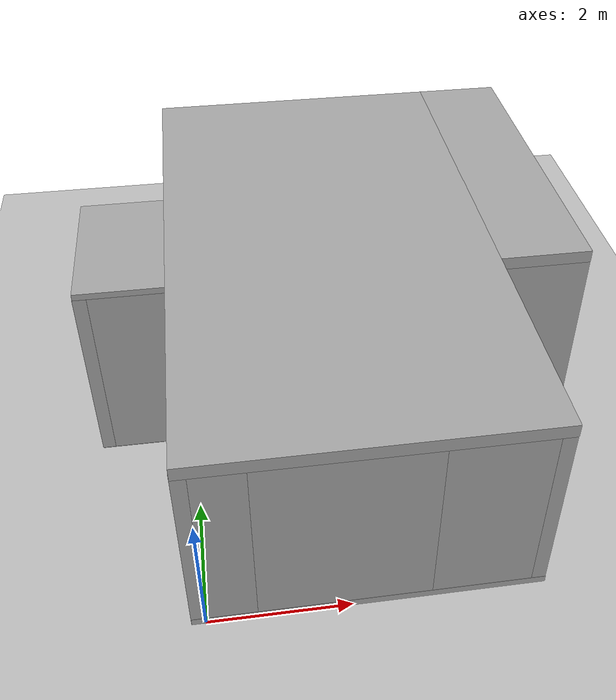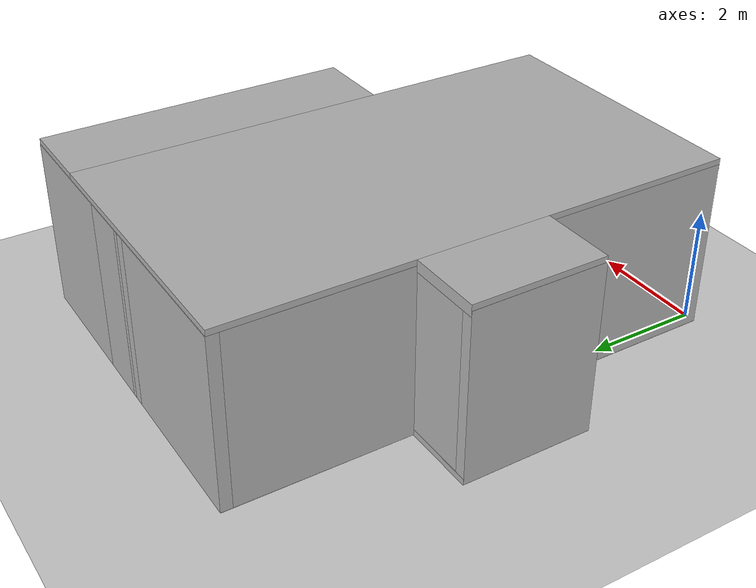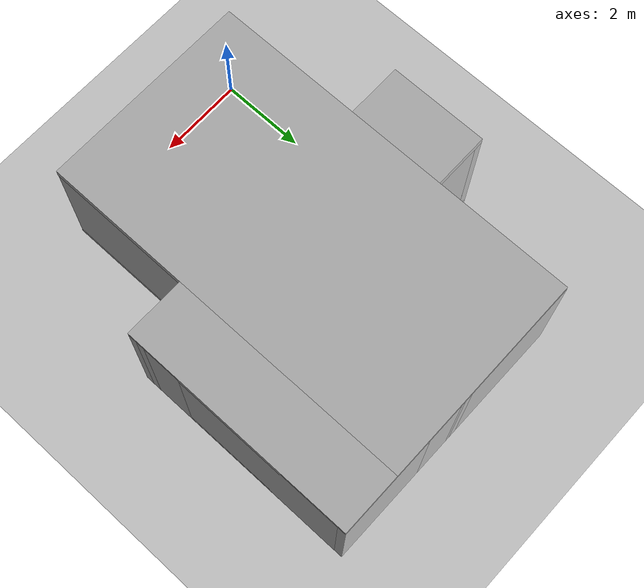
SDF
<sdf version="1.6">
 <world name="default">
  <light name="sun" type="directional">
   <pose>0 0 10 0 -0 0</pose>
   <diffuse>0.8 0.8 0.8 1</diffuse>
   <specular>0.1 0.1 0.1 1</specular>
   <attenuation>
    <range>1000</range>
    <constant>0.9</constant>
    <linear>0.01</linear>
    <quadratic>0.001</quadratic>
   </attenuation>
   <direction>-0.5 0.5 -1</direction>
  </light>
  <model name="ground_plane">
   <static>1</static>
   <link name="link">
    <collision name="collision">
     <geometry><plane><normal>0 0 1</normal><size>100 100</size></plane></geometry>
     <surface><friction><ode><mu>100</mu><mu2>50</mu2></ode></friction></surface>
    </collision>
    <visual name="visual">
     <cast_shadows>0</cast_shadows>
     <geometry><plane><normal>0 0 1</normal><size>100 100</size></plane></geometry>
     <material>
      <script><uri>file://media/materials/scripts/gazebo.material</uri><name>Gazebo/Grey</name></script>
     </material>
    </visual>
   </link>
  </model>
  <gravity>0 0 -9.8</gravity>
  <magnetic_field>6e-06 2.3e-05 -4.2e-05</magnetic_field>
  <atmosphere type="adiabatic"/>
  <physics name="default_physics" default="0" type="ode">
   <max_step_size>0.001</max_step_size>
   <real_time_factor>1</real_time_factor>
   <real_time_update_rate>1000</real_time_update_rate>
  </physics>
  <scene><ambient>0.4 0.4 0.4 1</ambient><background>0.7 0.7 0.7 1</background><shadows>1</shadows></scene>
  <spherical_coordinates>
   <surface_model>EARTH_WGS84</surface_model>
   <latitude_deg>0</latitude_deg>
   <longitude_deg>0</longitude_deg>
   <elevation>0</elevation>
   <heading_deg>0</heading_deg>
  </spherical_coordinates>
  <model name="sean_apartment_.7x_wall">
   <link name="link">
    <inertial>
     <mass>1</mass>
     <inertia>
      <ixx>0.166667</ixx>
      <ixy>0</ixy>
      <ixz>0</ixz>
      <iyy>0.166667</iyy>
      <iyz>0</iyz>
      <izz>0.166667</izz>
     </inertia>
    </inertial>
    <visual name="visual">
     <geometry><box><size>0.7 0.2 3</size></box></geometry>
     <material>
      <ambient>0.0 0.0 0.3 1</ambient>
      <diffuse>0.7 0.7 0.7 1</diffuse>
      <specular>0.01 0.01 0.01 1</specular>
      <emissive>0 0 0 1</emissive>
      <shader type="vertex"><normal_map>__default__</normal_map></shader>
     </material>
     <pose>0 0 1.5 0 -0 0</pose>
    </visual>
    <collision name="collision">
     <pose>0 0 1.5 0 -0 0</pose>
     <geometry><box><size>0.7 0.2 3</size></box></geometry>
     <surface>
      <friction>
       <ode><mu>1</mu><mu2>1</mu2><fdir1>0 0 0</fdir1><slip1>0</slip1><slip2>0</slip2></ode>
       <torsional>
        <coefficient>1</coefficient>
        <patch_radius>0</patch_radius>
        <surface_radius>0</surface_radius>
        <use_patch_radius>1</use_patch_radius>
        <ode><slip>0</slip></ode>
       </torsional>
      </friction>
      <bounce><restitution_coefficient>0</restitution_coefficient><threshold>1e+06</threshold></bounce>
      <contact>
       <collide_without_contact>0</collide_without_contact>
       <collide_without_contact_bitmask>1</collide_without_contact_bitmask>
       <collide_bitmask>1</collide_bitmask>
       <ode>
        <soft_cfm>0</soft_cfm>
        <soft_erp>0.2</soft_erp>
        <kp>1e+13</kp>
        <kd>1</kd>
        <max_vel>0.01</max_vel>
        <min_depth>0</min_depth>
       </ode>
       <bullet>
        <split_impulse>1</split_impulse>
        <split_impulse_penetration_threshold>-0.01</split_impulse_penetration_threshold>
        <soft_cfm>0</soft_cfm>
        <soft_erp>0.2</soft_erp>
        <kp>1e+13</kp>
        <kd>1</kd>
       </bullet>
      </contact>
     </surface>
    </collision>
   </link>
   <static>1</static>
   <pose>0.349997 0.100002 0 0 -0 4e-06</pose>
  </model>
  <model name="sean_apartment_2.4x_wall">
   <link name="link">
    <inertial>
     <mass>1</mass>
     <inertia>
      <ixx>0.166667</ixx>
      <ixy>0</ixy>
      <ixz>0</ixz>
      <iyy>0.166667</iyy>
      <iyz>0</iyz>
      <izz>0.166667</izz>
     </inertia>
    </inertial>
    <visual name="visual">
     <geometry><box><size>2.4 0.2 3</size></box></geometry>
     <material>
      <ambient>0.0 0.0 0.3 1</ambient>
      <diffuse>0.7 0.7 0.7 1</diffuse>
      <specular>0.01 0.01 0.01 1</specular>
      <emissive>0 0 0 1</emissive>
      <shader type="vertex"><normal_map>__default__</normal_map></shader>
     </material>
     <pose>0 0 1.5 0 -0 0</pose>
    </visual>
    <collision name="collision">
     <pose>0 0 1.5 0 -0 0</pose>
     <geometry><box><size>2.4 0.2 3</size></box></geometry>
     <surface>
      <friction>
       <ode><mu>1</mu><mu2>1</mu2><fdir1>0 0 0</fdir1><slip1>0</slip1><slip2>0</slip2></ode>
       <torsional>
        <coefficient>1</coefficient>
        <patch_radius>0</patch_radius>
        <surface_radius>0</surface_radius>
        <use_patch_radius>1</use_patch_radius>
        <ode><slip>0</slip></ode>
       </torsional>
      </friction>
      <bounce><restitution_coefficient>0</restitution_coefficient><threshold>1e+06</threshold></bounce>
      <contact>
       <collide_without_contact>0</collide_without_contact>
       <collide_without_contact_bitmask>1</collide_without_contact_bitmask>
       <collide_bitmask>1</collide_bitmask>
       <ode>
        <soft_cfm>0</soft_cfm>
        <soft_erp>0.2</soft_erp>
        <kp>1e+13</kp>
        <kd>1</kd>
        <max_vel>0.01</max_vel>
        <min_depth>0</min_depth>
       </ode>
       <bullet>
        <split_impulse>1</split_impulse>
        <split_impulse_penetration_threshold>-0.01</split_impulse_penetration_threshold>
        <soft_cfm>0</soft_cfm>
        <soft_erp>0.2</soft_erp>
        <kp>1e+13</kp>
        <kd>1</kd>
       </bullet>
      </contact>
     </surface>
    </collision>
   </link>
   <static>1</static>
   <pose>1.90002 0.09999 -0.00016 2e-06 -0.000134 -6e-06</pose>
  </model>
  <model name="sean_apartment_3.4y_wall">
   <link name="link">
    <inertial>
     <mass>1</mass>
     <inertia>
      <ixx>0.166667</ixx>
      <ixy>0</ixy>
      <ixz>0</ixz>
      <iyy>0.166667</iyy>
      <iyz>0</iyz>
      <izz>0.166667</izz>
     </inertia>
    </inertial>
    <visual name="visual">
     <geometry><box><size>0.2 3.4 3</size></box></geometry>
     <material>
      <ambient>0.0 0.0 0.3 1</ambient>
      <diffuse>0.7 0.7 0.7 1</diffuse>
      <specular>0.01 0.01 0.01 1</specular>
      <emissive>0 0 0 1</emissive>
      <shader type="vertex"><normal_map>__default__</normal_map></shader>
     </material>
     <pose>0 0 1.5 0 -0 0</pose>
    </visual>
    <collision name="collision">
     <pose>0 0 1.5 0 -0 0</pose>
     <geometry><box><size>0.2 3.4 3</size></box></geometry>
     <surface>
      <friction>
       <ode><mu>1</mu><mu2>1</mu2><fdir1>0 0 0</fdir1><slip1>0</slip1><slip2>0</slip2></ode>
       <torsional>
        <coefficient>1</coefficient>
        <patch_radius>0</patch_radius>
        <surface_radius>0</surface_radius>
        <use_patch_radius>1</use_patch_radius>
        <ode><slip>0</slip></ode>
       </torsional>
      </friction>
      <bounce><restitution_coefficient>0</restitution_coefficient><threshold>1e+06</threshold></bounce>
      <contact>
       <collide_without_contact>0</collide_without_contact>
       <collide_without_contact_bitmask>1</collide_without_contact_bitmask>
       <collide_bitmask>1</collide_bitmask>
       <ode>
        <soft_cfm>0</soft_cfm>
        <soft_erp>0.2</soft_erp>
        <kp>1e+13</kp>
        <kd>1</kd>
        <max_vel>0.01</max_vel>
        <min_depth>0</min_depth>
       </ode>
       <bullet>
        <split_impulse>1</split_impulse>
        <split_impulse_penetration_threshold>-0.01</split_impulse_penetration_threshold>
        <soft_cfm>0</soft_cfm>
        <soft_erp>0.2</soft_erp>
        <kp>1e+13</kp>
        <kd>1</kd>
       </bullet>
      </contact>
     </surface>
    </collision>
   </link>
   <static>1</static>
   <pose>4.60003 1.69995 -0.000688 0.000406 9e-06 1.8e-05</pose>
  </model>
  <model name="sean_apartment_1.4x_wall">
   <link name="link">
    <inertial>
     <mass>1</mass>
     <inertia>
      <ixx>0.166667</ixx>
      <ixy>0</ixy>
      <ixz>0</ixz>
      <iyy>0.166667</iyy>
      <iyz>0</iyz>
      <izz>0.166667</izz>
     </inertia>
    </inertial>
    <visual name="visual">
     <geometry><box><size>1.4 0.2 3</size></box></geometry>
     <material>
      <ambient>0.0 0.0 0.3 1</ambient>
      <diffuse>0.7 0.7 0.7 1</diffuse>
      <specular>0.01 0.01 0.01 1</specular>
      <emissive>0 0 0 1</emissive>
      <shader type="vertex"><normal_map>__default__</normal_map></shader>
     </material>
     <pose>0 0 1.5 0 -0 0</pose>
    </visual>
    <collision name="collision">
     <pose>0 0 1.5 0 -0 0</pose>
     <geometry><box><size>1.4 0.2 3</size></box></geometry>
     <surface>
      <friction>
       <ode><mu>1</mu><mu2>1</mu2><fdir1>0 0 0</fdir1><slip1>0</slip1><slip2>0</slip2></ode>
       <torsional>
        <coefficient>1</coefficient>
        <patch_radius>0</patch_radius>
        <surface_radius>0</surface_radius>
        <use_patch_radius>1</use_patch_radius>
        <ode><slip>0</slip></ode>
       </torsional>
      </friction>
      <bounce><restitution_coefficient>0</restitution_coefficient><threshold>1e+06</threshold></bounce>
      <contact>
       <collide_without_contact>0</collide_without_contact>
       <collide_without_contact_bitmask>1</collide_without_contact_bitmask>
       <collide_bitmask>1</collide_bitmask>
       <ode>
        <soft_cfm>0</soft_cfm>
        <soft_erp>0.2</soft_erp>
        <kp>1e+13</kp>
        <kd>1</kd>
        <max_vel>0.01</max_vel>
        <min_depth>0</min_depth>
       </ode>
       <bullet>
        <split_impulse>1</split_impulse>
        <split_impulse_penetration_threshold>-0.01</split_impulse_penetration_threshold>
        <soft_cfm>0</soft_cfm>
        <soft_erp>0.2</soft_erp>
        <kp>1e+13</kp>
        <kd>1</kd>
       </bullet>
      </contact>
     </surface>
    </collision>
   </link>
   <static>1</static>
   <pose>3.80002 0.099955 -1.4e-05 0 -2e-05 -3.9e-05</pose>
  </model>
  <model name="sean_ceiling">
   <link name="link">
    <pose>7.96507 7.76554 0 0 -0 0</pose>
    <inertial>
     <mass>1</mass>
     <inertia>
      <ixx>0.166667</ixx>
      <ixy>0</ixy>
      <ixz>0</ixz>
      <iyy>0.166667</iyy>
      <iyz>0</iyz>
      <izz>0.166667</izz>
     </inertia>
    </inertial>
    <visual name="visual">
     <geometry><box><size>4.9 8.9 0.2</size></box></geometry>
     <material>
      <ambient>0.0 0.3 0.0 1</ambient>
      <diffuse>0.7 0.7 0.7 1</diffuse>
      <specular>0.01 0.01 0.01 1</specular>
      <emissive>0 0 0 1</emissive>
      <shader type="vertex"><normal_map>__default__</normal_map></shader>
     </material>
    </visual>
    <collision name="collision">
     <geometry><box><size>4.9 8.9 0.2</size></box></geometry>
     <surface>
      <friction>
       <ode><mu>1</mu><mu2>1</mu2><fdir1>0 0 0</fdir1><slip1>0</slip1><slip2>0</slip2></ode>
       <torsional>
        <coefficient>1</coefficient>
        <patch_radius>0</patch_radius>
        <surface_radius>0</surface_radius>
        <use_patch_radius>1</use_patch_radius>
        <ode><slip>0</slip></ode>
       </torsional>
      </friction>
      <bounce><restitution_coefficient>0</restitution_coefficient><threshold>1e+06</threshold></bounce>
      <contact>
       <collide_without_contact>0</collide_without_contact>
       <collide_without_contact_bitmask>1</collide_without_contact_bitmask>
       <collide_bitmask>1</collide_bitmask>
       <ode>
        <soft_cfm>0</soft_cfm>
        <soft_erp>0.2</soft_erp>
        <kp>1e+13</kp>
        <kd>1</kd>
        <max_vel>0.01</max_vel>
        <min_depth>0</min_depth>
       </ode>
       <bullet>
        <split_impulse>1</split_impulse>
        <split_impulse_penetration_threshold>-0.01</split_impulse_penetration_threshold>
        <soft_cfm>0</soft_cfm>
        <soft_erp>0.2</soft_erp>
        <kp>1e+13</kp>
        <kd>1</kd>
       </bullet>
      </contact>
     </surface>
    </collision>
   </link>
   <link name="link_1">
    <pose>4.86729 7.87368 0 0 -0 0</pose>
    <inertial>
     <mass>1</mass>
     <inertia>
      <ixx>0.166667</ixx>
      <ixy>0</ixy>
      <ixz>0</ixz>
      <iyy>0.166667</iyy>
      <iyz>0</iyz>
      <izz>0.166667</izz>
     </inertia>
    </inertial>
    <visual name="visual">
     <geometry><box><size>1.3 2.3 0.2</size></box></geometry>
     <material>
      <lighting>1</lighting>
      <ambient>0.0 0.3 0.0 1</ambient>
      <diffuse>0.7 0.7 0.7 1</diffuse>
      <specular>0.01 0.01 0.01 1</specular>
      <emissive>0 0 0 1</emissive>
      <shader type="vertex"><normal_map>__default__</normal_map></shader>
     </material>
    </visual>
    <collision name="collision">
     <geometry><box><size>1.3 2.3 0.2</size></box></geometry>
     <surface>
      <friction>
       <ode><mu>1</mu><mu2>1</mu2><fdir1>0 0 0</fdir1><slip1>0</slip1><slip2>0</slip2></ode>
       <torsional>
        <coefficient>1</coefficient>
        <patch_radius>0</patch_radius>
        <surface_radius>0</surface_radius>
        <use_patch_radius>1</use_patch_radius>
        <ode><slip>0</slip></ode>
       </torsional>
      </friction>
      <bounce><restitution_coefficient>0</restitution_coefficient><threshold>1e+06</threshold></bounce>
      <contact>
       <collide_without_contact>0</collide_without_contact>
       <collide_without_contact_bitmask>1</collide_without_contact_bitmask>
       <collide_bitmask>1</collide_bitmask>
       <ode>
        <soft_cfm>0</soft_cfm>
        <soft_erp>0.2</soft_erp>
        <kp>1e+13</kp>
        <kd>1</kd>
        <max_vel>0.01</max_vel>
        <min_depth>0</min_depth>
       </ode>
       <bullet>
        <split_impulse>1</split_impulse>
        <split_impulse_penetration_threshold>-0.01</split_impulse_penetration_threshold>
        <soft_cfm>0</soft_cfm>
        <soft_erp>0.2</soft_erp>
        <kp>1e+13</kp>
        <kd>1</kd>
       </bullet>
      </contact>
     </surface>
    </collision>
   </link>
   <link name="link_2">
    <pose>11.1108 9.46554 0 0 -0 0</pose>
    <inertial>
     <mass>1</mass>
     <inertia>
      <ixx>0.166667</ixx>
      <ixy>0</ixy>
      <ixz>0</ixz>
      <iyy>0.166667</iyy>
      <iyz>0</iyz>
      <izz>0.166667</izz>
     </inertia>
    </inertial>
    <visual name="visual">
     <geometry><box><size>1.4 5.5 0.2</size></box></geometry>
     <material>
      <lighting>1</lighting>
      <ambient>0.0 0.3 0.0 1</ambient>
      <diffuse>0.7 0.7 0.7 1</diffuse>
      <specular>0.01 0.01 0.01 1</specular>
      <emissive>0 0 0 1</emissive>
      <shader type="vertex"><normal_map>__default__</normal_map></shader>
     </material>
    </visual>
    <collision name="collision">
     <geometry><box><size>1.4 5.5 0.2</size></box></geometry>
     <surface>
      <friction>
       <ode><mu>1</mu><mu2>1</mu2><fdir1>0 0 0</fdir1><slip1>0</slip1><slip2>0</slip2></ode>
       <torsional>
        <coefficient>1</coefficient>
        <patch_radius>0</patch_radius>
        <surface_radius>0</surface_radius>
        <use_patch_radius>1</use_patch_radius>
        <ode><slip>0</slip></ode>
       </torsional>
      </friction>
      <bounce><restitution_coefficient>0</restitution_coefficient><threshold>1e+06</threshold></bounce>
      <contact>
       <collide_without_contact>0</collide_without_contact>
       <collide_without_contact_bitmask>1</collide_without_contact_bitmask>
       <collide_bitmask>1</collide_bitmask>
       <ode>
        <soft_cfm>0</soft_cfm>
        <soft_erp>0.2</soft_erp>
        <kp>1e+13</kp>
        <kd>1</kd>
        <max_vel>0.01</max_vel>
        <min_depth>0</min_depth>
       </ode>
       <bullet>
        <split_impulse>1</split_impulse>
        <split_impulse_penetration_threshold>-0.01</split_impulse_penetration_threshold>
        <soft_cfm>0</soft_cfm>
        <soft_erp>0.2</soft_erp>
        <kp>1e+13</kp>
        <kd>1</kd>
       </bullet>
      </contact>
     </surface>
    </collision>
   </link>
   <static>1</static>
   <pose>-5.711 -3.322 3 0 -0 0</pose>
  </model>
  <model name="sean_apartment_3.6_wall_0">
   <link name="link">
    <inertial>
     <mass>1</mass>
     <inertia>
      <ixx>0.166667</ixx>
      <ixy>0</ixy>
      <ixz>0</ixz>
      <iyy>0.166667</iyy>
      <iyz>0</iyz>
      <izz>0.166667</izz>
     </inertia>
    </inertial>
    <visual name="visual">
     <geometry><box><size>0.2 3.6 3</size></box></geometry>
     <material>
      <ambient>0.0 0.0 0.3 1</ambient>
      <diffuse>0.7 0.7 0.7 1</diffuse>
      <specular>0.01 0.01 0.01 1</specular>
      <emissive>0 0 0 1</emissive>
      <shader type="vertex"><normal_map>__default__</normal_map></shader>
     </material>
     <pose>0 0 1.5 0 -0 0</pose>
    </visual>
    <collision name="collision">
     <pose>0 0 1.5 0 -0 0</pose>
     <geometry><box><size>0.2 3.6 3</size></box></geometry>
     <surface>
      <friction>
       <ode><mu>1</mu><mu2>1</mu2><fdir1>0 0 0</fdir1><slip1>0</slip1><slip2>0</slip2></ode>
       <torsional>
        <coefficient>1</coefficient>
        <patch_radius>0</patch_radius>
        <surface_radius>0</surface_radius>
        <use_patch_radius>1</use_patch_radius>
        <ode><slip>0</slip></ode>
       </torsional>
      </friction>
      <bounce><restitution_coefficient>0</restitution_coefficient><threshold>1e+06</threshold></bounce>
      <contact>
       <collide_without_contact>0</collide_without_contact>
       <collide_without_contact_bitmask>1</collide_without_contact_bitmask>
       <collide_bitmask>1</collide_bitmask>
       <ode>
        <soft_cfm>0</soft_cfm>
        <soft_erp>0.2</soft_erp>
        <kp>1e+13</kp>
        <kd>1</kd>
        <max_vel>0.01</max_vel>
        <min_depth>0</min_depth>
       </ode>
       <bullet>
        <split_impulse>1</split_impulse>
        <split_impulse_penetration_threshold>-0.01</split_impulse_penetration_threshold>
        <soft_cfm>0</soft_cfm>
        <soft_erp>0.2</soft_erp>
        <kp>1e+13</kp>
        <kd>1</kd>
       </bullet>
      </contact>
     </surface>
    </collision>
   </link>
   <static>1</static>
   <pose>-0.100031 1.8 -0.000872 -0.000486 -1.1e-05 -2.3e-05</pose>
  </model>
  <model name="sean_apartment_1.6x_wall_0">
   <link name="link">
    <inertial>
     <mass>1</mass>
     <inertia>
      <ixx>0.166667</ixx>
      <ixy>0</ixy>
      <ixz>0</ixz>
      <iyy>0.166667</iyy>
      <iyz>0</iyz>
      <izz>0.166667</izz>
     </inertia>
    </inertial>
    <visual name="visual">
     <geometry><box><size>1.6 0.2 3</size></box></geometry>
     <material>
      <ambient>0.0 0.0 0.3 1</ambient>
      <diffuse>0.7 0.7 0.7 1</diffuse>
      <specular>0.01 0.01 0.01 1</specular>
      <emissive>0 0 0 1</emissive>
      <shader type="vertex"><normal_map>__default__</normal_map></shader>
     </material>
     <pose>0 0 1.5 0 -0 0</pose>
    </visual>
    <collision name="collision">
     <pose>0 0 1.5 0 -0 0</pose>
     <geometry><box><size>1.6 0.2 3</size></box></geometry>
     <surface>
      <friction>
       <ode><mu>1</mu><mu2>1</mu2><fdir1>0 0 0</fdir1><slip1>0</slip1><slip2>0</slip2></ode>
       <torsional>
        <coefficient>1</coefficient>
        <patch_radius>0</patch_radius>
        <surface_radius>0</surface_radius>
        <use_patch_radius>1</use_patch_radius>
        <ode><slip>0</slip></ode>
       </torsional>
      </friction>
      <bounce><restitution_coefficient>0</restitution_coefficient><threshold>1e+06</threshold></bounce>
      <contact>
       <collide_without_contact>0</collide_without_contact>
       <collide_without_contact_bitmask>1</collide_without_contact_bitmask>
       <collide_bitmask>1</collide_bitmask>
       <ode>
        <soft_cfm>0</soft_cfm>
        <soft_erp>0.2</soft_erp>
        <kp>1e+13</kp>
        <kd>1</kd>
        <max_vel>0.01</max_vel>
        <min_depth>0</min_depth>
       </ode>
       <bullet>
        <split_impulse>1</split_impulse>
        <split_impulse_penetration_threshold>-0.01</split_impulse_penetration_threshold>
        <soft_cfm>0</soft_cfm>
        <soft_erp>0.2</soft_erp>
        <kp>1e+13</kp>
        <kd>1</kd>
       </bullet>
      </contact>
     </surface>
    </collision>
   </link>
   <static>1</static>
   <pose>5.30001 3.4999 -2.6e-05 -0 -3.3e-05 -0.000675</pose>
  </model>
  <model name="seans_apartment_.2x_wall">
   <link name="link">
    <inertial>
     <mass>1</mass>
     <inertia>
      <ixx>0.166667</ixx>
      <ixy>0</ixy>
      <ixz>0</ixz>
      <iyy>0.166667</iyy>
      <iyz>0</iyz>
      <izz>0.166667</izz>
     </inertia>
    </inertial>
    <visual name="visual">
     <geometry><box><size>0.2 0.2 3</size></box></geometry>
     <material>
      <ambient>0.0 0.0 0.3 1</ambient>
      <diffuse>0.7 0.7 0.7 1</diffuse>
      <specular>0.01 0.01 0.01 1</specular>
      <emissive>0 0 0 1</emissive>
      <shader type="vertex"><normal_map>__default__</normal_map></shader>
     </material>
     <pose>0 0 1.5 0 -0 0</pose>
    </visual>
    <collision name="collision">
     <pose>0 0 1.5 0 -0 0</pose>
     <geometry><box><size>0.2 0.2 3</size></box></geometry>
     <surface>
      <friction>
       <ode><mu>1</mu><mu2>1</mu2><fdir1>0 0 0</fdir1><slip1>0</slip1><slip2>0</slip2></ode>
       <torsional>
        <coefficient>1</coefficient>
        <patch_radius>0</patch_radius>
        <surface_radius>0</surface_radius>
        <use_patch_radius>1</use_patch_radius>
        <ode><slip>0</slip></ode>
       </torsional>
      </friction>
      <bounce><restitution_coefficient>0</restitution_coefficient><threshold>1e+06</threshold></bounce>
      <contact>
       <collide_without_contact>0</collide_without_contact>
       <collide_without_contact_bitmask>1</collide_without_contact_bitmask>
       <collide_bitmask>1</collide_bitmask>
       <ode>
        <soft_cfm>0</soft_cfm>
        <soft_erp>0.2</soft_erp>
        <kp>1e+13</kp>
        <kd>1</kd>
        <max_vel>0.01</max_vel>
        <min_depth>0</min_depth>
       </ode>
       <bullet>
        <split_impulse>1</split_impulse>
        <split_impulse_penetration_threshold>-0.01</split_impulse_penetration_threshold>
        <soft_cfm>0</soft_cfm>
        <soft_erp>0.2</soft_erp>
        <kp>1e+13</kp>
        <kd>1</kd>
       </bullet>
      </contact>
     </surface>
    </collision>
   </link>
   <static>1</static>
   <pose>6.00002 3.6996 -1e-06 -4e-06 -4e-06 -0.000242</pose>
  </model>
  <model name="sean_apartment_.9y_wall">
   <link name="link">
    <inertial>
     <mass>1</mass>
     <inertia>
      <ixx>0.166667</ixx>
      <ixy>0</ixy>
      <ixz>0</ixz>
      <iyy>0.166667</iyy>
      <iyz>0</iyz>
      <izz>0.166667</izz>
     </inertia>
    </inertial>
    <visual name="visual">
     <geometry><box><size>0.2 0.9 3</size></box></geometry>
     <material>
      <ambient>0.0 0.0 0.3 1</ambient>
      <diffuse>0.7 0.7 0.7 1</diffuse>
      <specular>0.01 0.01 0.01 1</specular>
      <emissive>0 0 0 1</emissive>
      <shader type="vertex"><normal_map>__default__</normal_map></shader>
     </material>
     <pose>0 0 1.5 0 -0 0</pose>
    </visual>
    <collision name="collision">
     <pose>0 0 1.5 0 -0 0</pose>
     <geometry><box><size>0.2 0.9 3</size></box></geometry>
     <surface>
      <friction>
       <ode><mu>1</mu><mu2>1</mu2><fdir1>0 0 0</fdir1><slip1>0</slip1><slip2>0</slip2></ode>
       <torsional>
        <coefficient>1</coefficient>
        <patch_radius>0</patch_radius>
        <surface_radius>0</surface_radius>
        <use_patch_radius>1</use_patch_radius>
        <ode><slip>0</slip></ode>
       </torsional>
      </friction>
      <bounce><restitution_coefficient>0</restitution_coefficient><threshold>1e+06</threshold></bounce>
      <contact>
       <collide_without_contact>0</collide_without_contact>
       <collide_without_contact_bitmask>1</collide_without_contact_bitmask>
       <collide_bitmask>1</collide_bitmask>
       <ode>
        <soft_cfm>0</soft_cfm>
        <soft_erp>0.2</soft_erp>
        <kp>1e+13</kp>
        <kd>1</kd>
        <max_vel>0.01</max_vel>
        <min_depth>0</min_depth>
       </ode>
       <bullet>
        <split_impulse>1</split_impulse>
        <split_impulse_penetration_threshold>-0.01</split_impulse_penetration_threshold>
        <soft_cfm>0</soft_cfm>
        <soft_erp>0.2</soft_erp>
        <kp>1e+13</kp>
        <kd>1</kd>
       </bullet>
      </contact>
     </surface>
    </collision>
   </link>
   <static>1</static>
   <pose>6.00004 4.24963 -2e-06 4e-06 -0 -0.000245</pose>
  </model>
  <model name="sean_apartment_4.0y_wall_0">
   <link name="link">
    <inertial>
     <mass>1</mass>
     <inertia>
      <ixx>0.166667</ixx>
      <ixy>0</ixy>
      <ixz>0</ixz>
      <iyy>0.166667</iyy>
      <iyz>0</iyz>
      <izz>0.166667</izz>
     </inertia>
    </inertial>
    <visual name="visual">
     <geometry><box><size>0.2 4 3</size></box></geometry>
     <material>
      <ambient>0.0 0.0 0.3 1</ambient>
      <diffuse>0.7 0.7 0.7 1</diffuse>
      <specular>0.01 0.01 0.01 1</specular>
      <emissive>0 0 0 1</emissive>
      <shader type="vertex"><normal_map>__default__</normal_map></shader>
     </material>
     <pose>0 0 1.5 0 -0 0</pose>
    </visual>
    <collision name="collision">
     <pose>0 0 1.5 0 -0 0</pose>
     <geometry><box><size>0.2 4 3</size></box></geometry>
     <surface>
      <friction>
       <ode><mu>1</mu><mu2>1</mu2><fdir1>0 0 0</fdir1><slip1>0</slip1><slip2>0</slip2></ode>
       <torsional>
        <coefficient>1</coefficient>
        <patch_radius>0</patch_radius>
        <surface_radius>0</surface_radius>
        <use_patch_radius>1</use_patch_radius>
        <ode><slip>0</slip></ode>
       </torsional>
      </friction>
      <bounce><restitution_coefficient>0</restitution_coefficient><threshold>1e+06</threshold></bounce>
      <contact>
       <collide_without_contact>0</collide_without_contact>
       <collide_without_contact_bitmask>1</collide_without_contact_bitmask>
       <collide_bitmask>1</collide_bitmask>
       <ode>
        <soft_cfm>0</soft_cfm>
        <soft_erp>0.2</soft_erp>
        <kp>1e+13</kp>
        <kd>1</kd>
        <max_vel>0.01</max_vel>
        <min_depth>0</min_depth>
       </ode>
       <bullet>
        <split_impulse>1</split_impulse>
        <split_impulse_penetration_threshold>-0.01</split_impulse_penetration_threshold>
        <soft_cfm>0</soft_cfm>
        <soft_erp>0.2</soft_erp>
        <kp>1e+13</kp>
        <kd>1</kd>
       </bullet>
      </contact>
     </surface>
    </collision>
   </link>
   <static>1</static>
   <pose>5.99872 6.69979 -4e-06 -2e-06 -9e-06 -0.001862</pose>
  </model>
  <model name="sean_apartment_2.3x_wall_1">
   <link name="link">
    <inertial>
     <mass>1</mass>
     <inertia>
      <ixx>0.166667</ixx>
      <ixy>0</ixy>
      <ixz>0</ixz>
      <iyy>0.166667</iyy>
      <iyz>0</iyz>
      <izz>0.166667</izz>
     </inertia>
    </inertial>
    <visual name="visual">
     <geometry><box><size>2.3 0.2 3</size></box></geometry>
     <material>
      <ambient>0.0 0.0 0.3 1</ambient>
      <diffuse>0.7 0.7 0.7 1</diffuse>
      <specular>0.01 0.01 0.01 1</specular>
      <emissive>0 0 0 1</emissive>
      <shader type="vertex"><normal_map>__default__</normal_map></shader>
     </material>
     <pose>0 0 1.5 0 -0 0</pose>
    </visual>
    <collision name="collision">
     <pose>0 0 1.5 0 -0 0</pose>
     <geometry><box><size>2.3 0.2 3</size></box></geometry>
     <surface>
      <friction>
       <ode><mu>1</mu><mu2>1</mu2><fdir1>0 0 0</fdir1><slip1>0</slip1><slip2>0</slip2></ode>
       <torsional>
        <coefficient>1</coefficient>
        <patch_radius>0</patch_radius>
        <surface_radius>0</surface_radius>
        <use_patch_radius>1</use_patch_radius>
        <ode><slip>0</slip></ode>
       </torsional>
      </friction>
      <bounce><restitution_coefficient>0</restitution_coefficient><threshold>1e+06</threshold></bounce>
      <contact>
       <collide_without_contact>0</collide_without_contact>
       <collide_without_contact_bitmask>1</collide_without_contact_bitmask>
       <collide_bitmask>1</collide_bitmask>
       <ode>
        <soft_cfm>0</soft_cfm>
        <soft_erp>0.2</soft_erp>
        <kp>1e+13</kp>
        <kd>1</kd>
        <max_vel>0.01</max_vel>
        <min_depth>0</min_depth>
       </ode>
       <bullet>
        <split_impulse>1</split_impulse>
        <split_impulse_penetration_threshold>-0.01</split_impulse_penetration_threshold>
        <soft_cfm>0</soft_cfm>
        <soft_erp>0.2</soft_erp>
        <kp>1e+13</kp>
        <kd>1</kd>
       </bullet>
      </contact>
     </surface>
    </collision>
   </link>
   <static>1</static>
   <pose>4.95003 8.80005 -0.000112 1e-06 9.8e-05 0.000104</pose>
  </model>
  <model name="sean_apartment_.9y_wall_0">
   <link name="link">
    <inertial>
     <mass>1</mass>
     <inertia>
      <ixx>0.166667</ixx>
      <ixy>0</ixy>
      <ixz>0</ixz>
      <iyy>0.166667</iyy>
      <iyz>0</iyz>
      <izz>0.166667</izz>
     </inertia>
    </inertial>
    <visual name="visual">
     <geometry><box><size>0.2 0.9 3</size></box></geometry>
     <material>
      <ambient>0.0 0.0 0.3 1</ambient>
      <diffuse>0.7 0.7 0.7 1</diffuse>
      <specular>0.01 0.01 0.01 1</specular>
      <emissive>0 0 0 1</emissive>
      <shader type="vertex"><normal_map>__default__</normal_map></shader>
     </material>
     <pose>0 0 1.5 0 -0 0</pose>
    </visual>
    <collision name="collision">
     <pose>0 0 1.5 0 -0 0</pose>
     <geometry><box><size>0.2 0.9 3</size></box></geometry>
     <surface>
      <friction>
       <ode><mu>1</mu><mu2>1</mu2><fdir1>0 0 0</fdir1><slip1>0</slip1><slip2>0</slip2></ode>
       <torsional>
        <coefficient>1</coefficient>
        <patch_radius>0</patch_radius>
        <surface_radius>0</surface_radius>
        <use_patch_radius>1</use_patch_radius>
        <ode><slip>0</slip></ode>
       </torsional>
      </friction>
      <bounce><restitution_coefficient>0</restitution_coefficient><threshold>1e+06</threshold></bounce>
      <contact>
       <collide_without_contact>0</collide_without_contact>
       <collide_without_contact_bitmask>1</collide_without_contact_bitmask>
       <collide_bitmask>1</collide_bitmask>
       <ode>
        <soft_cfm>0</soft_cfm>
        <soft_erp>0.2</soft_erp>
        <kp>1e+13</kp>
        <kd>1</kd>
        <max_vel>0.01</max_vel>
        <min_depth>0</min_depth>
       </ode>
       <bullet>
        <split_impulse>1</split_impulse>
        <split_impulse_penetration_threshold>-0.01</split_impulse_penetration_threshold>
        <soft_cfm>0</soft_cfm>
        <soft_erp>0.2</soft_erp>
        <kp>1e+13</kp>
        <kd>1</kd>
       </bullet>
      </contact>
     </surface>
    </collision>
   </link>
   <static>1</static>
   <pose>3.34999 8.80001 -6e-06 -1.2e-05 -0 -1.5708</pose>
  </model>
  <model name="sean_floor">
   <link name="link">
    <pose>7.96507 7.76554 0 0 -0 0</pose>
    <inertial>
     <mass>1</mass>
     <inertia>
      <ixx>0.166667</ixx>
      <ixy>0</ixy>
      <ixz>0</ixz>
      <iyy>0.166667</iyy>
      <iyz>0</iyz>
      <izz>0.166667</izz>
     </inertia>
    </inertial>
    <visual name="visual">
     <geometry><box><size>4.9 8.9 0.2</size></box></geometry>
     <material>
      <ambient>0.3 0.0 0.3 1</ambient>
      <diffuse>0.7 0.7 0.7 1</diffuse>
      <specular>0.01 0.01 0.01 1</specular>
      <emissive>0 0 0 1</emissive>
      <shader type="vertex"><normal_map>__default__</normal_map></shader>
     </material>
    </visual>
    <collision name="collision">
     <geometry><box><size>4.9 8.9 0.2</size></box></geometry>
     <surface>
      <friction>
       <ode><mu>1</mu><mu2>1</mu2><fdir1>0 0 0</fdir1><slip1>0</slip1><slip2>0</slip2></ode>
       <torsional>
        <coefficient>1</coefficient>
        <patch_radius>0</patch_radius>
        <surface_radius>0</surface_radius>
        <use_patch_radius>1</use_patch_radius>
        <ode><slip>0</slip></ode>
       </torsional>
      </friction>
      <bounce><restitution_coefficient>0</restitution_coefficient><threshold>1e+06</threshold></bounce>
      <contact>
       <collide_without_contact>0</collide_without_contact>
       <collide_without_contact_bitmask>1</collide_without_contact_bitmask>
       <collide_bitmask>1</collide_bitmask>
       <ode>
        <soft_cfm>0</soft_cfm>
        <soft_erp>0.2</soft_erp>
        <kp>1e+13</kp>
        <kd>1</kd>
        <max_vel>0.01</max_vel>
        <min_depth>0</min_depth>
       </ode>
       <bullet>
        <split_impulse>1</split_impulse>
        <split_impulse_penetration_threshold>-0.01</split_impulse_penetration_threshold>
        <soft_cfm>0</soft_cfm>
        <soft_erp>0.2</soft_erp>
        <kp>1e+13</kp>
        <kd>1</kd>
       </bullet>
      </contact>
     </surface>
    </collision>
   </link>
   <link name="link_1">
    <pose>4.86729 7.87368 0 0 -0 0</pose>
    <inertial>
     <mass>1</mass>
     <inertia>
      <ixx>0.166667</ixx>
      <ixy>0</ixy>
      <ixz>0</ixz>
      <iyy>0.166667</iyy>
      <iyz>0</iyz>
      <izz>0.166667</izz>
     </inertia>
    </inertial>
    <visual name="visual">
     <geometry><box><size>1.3 2.3 0.2</size></box></geometry>
     <material>
      <lighting>1</lighting>
      <ambient>0.3 0.0 0.3 1</ambient>
      <diffuse>0.7 0.7 0.7 1</diffuse>
      <specular>0.01 0.01 0.01 1</specular>
      <emissive>0 0 0 1</emissive>
      <shader type="vertex"><normal_map>__default__</normal_map></shader>
     </material>
    </visual>
    <collision name="collision">
     <geometry><box><size>1.3 2.3 0.2</size></box></geometry>
     <surface>
      <friction>
       <ode><mu>1</mu><mu2>1</mu2><fdir1>0 0 0</fdir1><slip1>0</slip1><slip2>0</slip2></ode>
       <torsional>
        <coefficient>1</coefficient>
        <patch_radius>0</patch_radius>
        <surface_radius>0</surface_radius>
        <use_patch_radius>1</use_patch_radius>
        <ode><slip>0</slip></ode>
       </torsional>
      </friction>
      <bounce><restitution_coefficient>0</restitution_coefficient><threshold>1e+06</threshold></bounce>
      <contact>
       <collide_without_contact>0</collide_without_contact>
       <collide_without_contact_bitmask>1</collide_without_contact_bitmask>
       <collide_bitmask>1</collide_bitmask>
       <ode>
        <soft_cfm>0</soft_cfm>
        <soft_erp>0.2</soft_erp>
        <kp>1e+13</kp>
        <kd>1</kd>
        <max_vel>0.01</max_vel>
        <min_depth>0</min_depth>
       </ode>
       <bullet>
        <split_impulse>1</split_impulse>
        <split_impulse_penetration_threshold>-0.01</split_impulse_penetration_threshold>
        <soft_cfm>0</soft_cfm>
        <soft_erp>0.2</soft_erp>
        <kp>1e+13</kp>
        <kd>1</kd>
       </bullet>
      </contact>
     </surface>
    </collision>
   </link>
   <link name="link_2">
    <pose>11.1108 9.46554 0 0 -0 0</pose>
    <inertial>
     <mass>1</mass>
     <inertia>
      <ixx>0.166667</ixx>
      <ixy>0</ixy>
      <ixz>0</ixz>
      <iyy>0.166667</iyy>
      <iyz>0</iyz>
      <izz>0.166667</izz>
     </inertia>
    </inertial>
    <visual name="visual">
     <geometry><box><size>1.4 5.5 0.2</size></box></geometry>
     <material>
      <lighting>1</lighting>
      <ambient>0.3 0.0 0.3 1</ambient>
      <diffuse>0.7 0.7 0.7 1</diffuse>
      <specular>0.01 0.01 0.01 1</specular>
      <emissive>0 0 0 1</emissive>
      <shader type="vertex"><normal_map>__default__</normal_map></shader>
     </material>
    </visual>
    <collision name="collision">
     <geometry><box><size>1.4 5.5 0.2</size></box></geometry>
     <surface>
      <friction>
       <ode><mu>1</mu><mu2>1</mu2><fdir1>0 0 0</fdir1><slip1>0</slip1><slip2>0</slip2></ode>
       <torsional>
        <coefficient>1</coefficient>
        <patch_radius>0</patch_radius>
        <surface_radius>0</surface_radius>
        <use_patch_radius>1</use_patch_radius>
        <ode><slip>0</slip></ode>
       </torsional>
      </friction>
      <bounce><restitution_coefficient>0</restitution_coefficient><threshold>1e+06</threshold></bounce>
      <contact>
       <collide_without_contact>0</collide_without_contact>
       <collide_without_contact_bitmask>1</collide_without_contact_bitmask>
       <collide_bitmask>1</collide_bitmask>
       <ode>
        <soft_cfm>0</soft_cfm>
        <soft_erp>0.2</soft_erp>
        <kp>1e+13</kp>
        <kd>1</kd>
        <max_vel>0.01</max_vel>
        <min_depth>0</min_depth>
       </ode>
       <bullet>
        <split_impulse>1</split_impulse>
        <split_impulse_penetration_threshold>-0.01</split_impulse_penetration_threshold>
        <soft_cfm>0</soft_cfm>
        <soft_erp>0.2</soft_erp>
        <kp>1e+13</kp>
        <kd>1</kd>
       </bullet>
      </contact>
     </surface>
    </collision>
   </link>
   <static>1</static>
   <pose>-5.71166 -3.32189 0 0 -0 0</pose>
  </model>
  <model name="seans_apartment_.1x_wall_0">
   <link name="link">
    <inertial>
     <mass>1</mass>
     <inertia>
      <ixx>0.166667</ixx>
      <ixy>0</ixy>
      <ixz>0</ixz>
      <iyy>0.166667</iyy>
      <iyz>0</iyz>
      <izz>0.166667</izz>
     </inertia>
    </inertial>
    <visual name="visual">
     <geometry><box><size>0.1 0.2 3</size></box></geometry>
     <material>
      <ambient>0.0 0.0 0.3 1</ambient>
      <diffuse>0.7 0.7 0.7 1</diffuse>
      <specular>0.01 0.01 0.01 1</specular>
      <emissive>0 0 0 1</emissive>
      <shader type="vertex"><normal_map>__default__</normal_map></shader>
     </material>
     <pose>0 0 1.5 0 -0 0</pose>
    </visual>
    <collision name="collision">
     <pose>0 0 1.5 0 -0 0</pose>
     <geometry><box><size>0.1 0.2 3</size></box></geometry>
     <surface>
      <friction>
       <ode><mu>1</mu><mu2>1</mu2><fdir1>0 0 0</fdir1><slip1>0</slip1><slip2>0</slip2></ode>
       <torsional>
        <coefficient>1</coefficient>
        <patch_radius>0</patch_radius>
        <surface_radius>0</surface_radius>
        <use_patch_radius>1</use_patch_radius>
        <ode><slip>0</slip></ode>
       </torsional>
      </friction>
      <bounce><restitution_coefficient>0</restitution_coefficient><threshold>1e+06</threshold></bounce>
      <contact>
       <collide_without_contact>0</collide_without_contact>
       <collide_without_contact_bitmask>1</collide_without_contact_bitmask>
       <collide_bitmask>1</collide_bitmask>
       <ode>
        <soft_cfm>0</soft_cfm>
        <soft_erp>0.2</soft_erp>
        <kp>1e+13</kp>
        <kd>1</kd>
        <max_vel>0.01</max_vel>
        <min_depth>0</min_depth>
       </ode>
       <bullet>
        <split_impulse>1</split_impulse>
        <split_impulse_penetration_threshold>-0.01</split_impulse_penetration_threshold>
        <soft_cfm>0</soft_cfm>
        <soft_erp>0.2</soft_erp>
        <kp>1e+13</kp>
        <kd>1</kd>
       </bullet>
      </contact>
     </surface>
    </collision>
   </link>
   <static>1</static>
   <pose>2.84999 8.8 0 1e-06 -0 -3e-06</pose>
  </model>
  <model name="seans_apartment_1.0y_wall_0">
   <link name="link">
    <inertial>
     <mass>1</mass>
     <inertia>
      <ixx>0.166667</ixx>
      <ixy>0</ixy>
      <ixz>0</ixz>
      <iyy>0.166667</iyy>
      <iyz>0</iyz>
      <izz>0.166667</izz>
     </inertia>
    </inertial>
    <visual name="visual">
     <geometry><box><size>0.2 1 3</size></box></geometry>
     <material>
      <ambient>0.0 0.0 0.3 1</ambient>
      <diffuse>0.7 0.7 0.7 1</diffuse>
      <specular>0.01 0.01 0.01 1</specular>
      <emissive>0 0 0 1</emissive>
      <shader type="vertex"><normal_map>__default__</normal_map></shader>
     </material>
     <pose>0 0 1.5 0 -0 0</pose>
    </visual>
    <collision name="collision">
     <pose>0 0 1.5 0 -0 0</pose>
     <geometry><box><size>0.2 1 3</size></box></geometry>
     <surface>
      <friction>
       <ode><mu>1</mu><mu2>1</mu2><fdir1>0 0 0</fdir1><slip1>0</slip1><slip2>0</slip2></ode>
       <torsional>
        <coefficient>1</coefficient>
        <patch_radius>0</patch_radius>
        <surface_radius>0</surface_radius>
        <use_patch_radius>1</use_patch_radius>
        <ode><slip>0</slip></ode>
       </torsional>
      </friction>
      <bounce><restitution_coefficient>0</restitution_coefficient><threshold>1e+06</threshold></bounce>
      <contact>
       <collide_without_contact>0</collide_without_contact>
       <collide_without_contact_bitmask>1</collide_without_contact_bitmask>
       <collide_bitmask>1</collide_bitmask>
       <ode>
        <soft_cfm>0</soft_cfm>
        <soft_erp>0.2</soft_erp>
        <kp>1e+13</kp>
        <kd>1</kd>
        <max_vel>0.01</max_vel>
        <min_depth>0</min_depth>
       </ode>
       <bullet>
        <split_impulse>1</split_impulse>
        <split_impulse_penetration_threshold>-0.01</split_impulse_penetration_threshold>
        <soft_cfm>0</soft_cfm>
        <soft_erp>0.2</soft_erp>
        <kp>1e+13</kp>
        <kd>1</kd>
       </bullet>
      </contact>
     </surface>
    </collision>
   </link>
   <static>1</static>
   <pose>2.69999 8.4 -5e-06 -1e-05 -0 -5e-06</pose>
  </model>
  <model name="sean_apartment_2.8x_wall_0">
   <link name="link">
    <inertial>
     <mass>1</mass>
     <inertia>
      <ixx>0.166667</ixx>
      <ixy>0</ixy>
      <ixz>0</ixz>
      <iyy>0.166667</iyy>
      <iyz>0</iyz>
      <izz>0.166667</izz>
     </inertia>
    </inertial>
    <visual name="visual">
     <geometry><box><size>2.8 0.2 3</size></box></geometry>
     <material>
      <ambient>0.0 0.0 0.3 1</ambient>
      <diffuse>0.7 0.7 0.7 1</diffuse>
      <specular>0.01 0.01 0.01 1</specular>
      <emissive>0 0 0 1</emissive>
      <shader type="vertex"><normal_map>__default__</normal_map></shader>
     </material>
     <pose>0 0 1.5 0 -0 0</pose>
    </visual>
    <collision name="collision">
     <pose>0 0 1.5 0 -0 0</pose>
     <geometry><box><size>2.8 0.2 3</size></box></geometry>
     <surface>
      <friction>
       <ode><mu>1</mu><mu2>1</mu2><fdir1>0 0 0</fdir1><slip1>0</slip1><slip2>0</slip2></ode>
       <torsional>
        <coefficient>1</coefficient>
        <patch_radius>0</patch_radius>
        <surface_radius>0</surface_radius>
        <use_patch_radius>1</use_patch_radius>
        <ode><slip>0</slip></ode>
       </torsional>
      </friction>
      <bounce><restitution_coefficient>0</restitution_coefficient><threshold>1e+06</threshold></bounce>
      <contact>
       <collide_without_contact>0</collide_without_contact>
       <collide_without_contact_bitmask>1</collide_without_contact_bitmask>
       <collide_bitmask>1</collide_bitmask>
       <ode>
        <soft_cfm>0</soft_cfm>
        <soft_erp>0.2</soft_erp>
        <kp>1e+13</kp>
        <kd>1</kd>
        <max_vel>0.01</max_vel>
        <min_depth>0</min_depth>
       </ode>
       <bullet>
        <split_impulse>1</split_impulse>
        <split_impulse_penetration_threshold>-0.01</split_impulse_penetration_threshold>
        <soft_cfm>0</soft_cfm>
        <soft_erp>0.2</soft_erp>
        <kp>1e+13</kp>
        <kd>1</kd>
       </bullet>
      </contact>
     </surface>
    </collision>
   </link>
   <static>1</static>
   <pose>1.19997 8.80029 0 0 0 -0.00023</pose>
  </model>
  <model name="sean_apartment_4.2y_wall_0">
   <link name="link">
    <inertial>
     <mass>1</mass>
     <inertia>
      <ixx>0.166667</ixx>
      <ixy>0</ixy>
      <ixz>0</ixz>
      <iyy>0.166667</iyy>
      <iyz>0</iyz>
      <izz>0.166667</izz>
     </inertia>
    </inertial>
    <visual name="visual">
     <geometry><box><size>0.2 4.2 3</size></box></geometry>
     <material>
      <ambient>0.0 0.0 0.3 1</ambient>
      <diffuse>0.7 0.7 0.7 1</diffuse>
      <specular>0.01 0.01 0.01 1</specular>
      <emissive>0 0 0 1</emissive>
      <shader type="vertex"><normal_map>__default__</normal_map></shader>
     </material>
     <pose>0 0 1.5 0 -0 0</pose>
    </visual>
    <collision name="collision">
     <pose>0 0 1.5 0 -0 0</pose>
     <geometry><box><size>0.2 4.2 3</size></box></geometry>
     <surface>
      <friction>
       <ode><mu>1</mu><mu2>1</mu2><fdir1>0 0 0</fdir1><slip1>0</slip1><slip2>0</slip2></ode>
       <torsional>
        <coefficient>1</coefficient>
        <patch_radius>0</patch_radius>
        <surface_radius>0</surface_radius>
        <use_patch_radius>1</use_patch_radius>
        <ode><slip>0</slip></ode>
       </torsional>
      </friction>
      <bounce><restitution_coefficient>0</restitution_coefficient><threshold>1e+06</threshold></bounce>
      <contact>
       <collide_without_contact>0</collide_without_contact>
       <collide_without_contact_bitmask>1</collide_without_contact_bitmask>
       <collide_bitmask>1</collide_bitmask>
       <ode>
        <soft_cfm>0</soft_cfm>
        <soft_erp>0.2</soft_erp>
        <kp>1e+13</kp>
        <kd>1</kd>
        <max_vel>0.01</max_vel>
        <min_depth>0</min_depth>
       </ode>
       <bullet>
        <split_impulse>1</split_impulse>
        <split_impulse_penetration_threshold>-0.01</split_impulse_penetration_threshold>
        <soft_cfm>0</soft_cfm>
        <soft_erp>0.2</soft_erp>
        <kp>1e+13</kp>
        <kd>1</kd>
       </bullet>
      </contact>
     </surface>
    </collision>
   </link>
   <static>1</static>
   <pose>-0.103967 6.60027 -4e-06 2e-06 -9e-06 -0.002424</pose>
  </model>
  <model name="sean_apartment_kitchen_cabinet_1">
   <link name="link">
    <inertial>
     <mass>1</mass>
     <inertia>
      <ixx>0.166667</ixx>
      <ixy>0</ixy>
      <ixz>0</ixz>
      <iyy>0.166667</iyy>
      <iyz>0</iyz>
      <izz>0.166667</izz>
     </inertia>
    </inertial>
    <visual name="visual">
     <geometry><box><size>0.6 0.8 1</size></box></geometry>
     <material>
      <ambient>0.6 0.6 0.0 1</ambient>
      <diffuse>0.7 0.7 0.7 1</diffuse>
      <specular>0.01 0.01 0.01 1</specular>
      <emissive>0 0 0 1</emissive>
      <shader type="vertex"><normal_map>__default__</normal_map></shader>
     </material>
     <pose>0 0 0.5 0 -0 0</pose>
    </visual>
    <collision name="collision">
     <pose>0 0 0.5 0 -0 0</pose>
     <geometry><box><size>0.6 0.8 1</size></box></geometry>
     <surface>
      <friction>
       <ode><mu>1</mu><mu2>1</mu2><fdir1>0 0 0</fdir1><slip1>0</slip1><slip2>0</slip2></ode>
       <torsional>
        <coefficient>1</coefficient>
        <patch_radius>0</patch_radius>
        <surface_radius>0</surface_radius>
        <use_patch_radius>1</use_patch_radius>
        <ode><slip>0</slip></ode>
       </torsional>
      </friction>
      <bounce><restitution_coefficient>0</restitution_coefficient><threshold>1e+06</threshold></bounce>
      <contact>
       <collide_without_contact>0</collide_without_contact>
       <collide_without_contact_bitmask>1</collide_without_contact_bitmask>
       <collide_bitmask>1</collide_bitmask>
       <ode>
        <soft_cfm>0</soft_cfm>
        <soft_erp>0.2</soft_erp>
        <kp>1e+13</kp>
        <kd>1</kd>
        <max_vel>0.01</max_vel>
        <min_depth>0</min_depth>
       </ode>
       <bullet>
        <split_impulse>1</split_impulse>
        <split_impulse_penetration_threshold>-0.01</split_impulse_penetration_threshold>
        <soft_cfm>0</soft_cfm>
        <soft_erp>0.2</soft_erp>
        <kp>1e+13</kp>
        <kd>1</kd>
       </bullet>
      </contact>
     </surface>
    </collision>
   </link>
   <static>1</static>
   <pose>0.300745 8.2996 0 0 0 -0.001191</pose>
  </model>
  <model name="sean_apartment_kitchen_cabinet_2">
   <link name="link">
    <inertial>
     <mass>1</mass>
     <inertia>
      <ixx>0.166667</ixx>
      <ixy>0</ixy>
      <ixz>0</ixz>
      <iyy>0.166667</iyy>
      <iyz>0</iyz>
      <izz>0.166667</izz>
     </inertia>
    </inertial>
    <visual name="visual">
     <geometry><box><size>0.6 0.8 1</size></box></geometry>
     <material>
      <ambient>0.6 0.6 0.0 1</ambient>
      <diffuse>0.7 0.7 0.7 1</diffuse>
      <specular>0.01 0.01 0.01 1</specular>
      <emissive>0 0 0 1</emissive>
      <shader type="vertex"><normal_map>__default__</normal_map></shader>
     </material>
     <pose>0 0 0.5 0 -0 0</pose>
    </visual>
    <collision name="collision">
     <pose>0 0 0.5 0 -0 0</pose>
     <geometry><box><size>0.6 0.8 1</size></box></geometry>
     <surface>
      <friction>
       <ode><mu>1</mu><mu2>1</mu2><fdir1>0 0 0</fdir1><slip1>0</slip1><slip2>0</slip2></ode>
       <torsional>
        <coefficient>1</coefficient>
        <patch_radius>0</patch_radius>
        <surface_radius>0</surface_radius>
        <use_patch_radius>1</use_patch_radius>
        <ode><slip>0</slip></ode>
       </torsional>
      </friction>
      <bounce><restitution_coefficient>0</restitution_coefficient><threshold>1e+06</threshold></bounce>
      <contact>
       <collide_without_contact>0</collide_without_contact>
       <collide_without_contact_bitmask>1</collide_without_contact_bitmask>
       <collide_bitmask>1</collide_bitmask>
       <ode>
        <soft_cfm>0</soft_cfm>
        <soft_erp>0.2</soft_erp>
        <kp>1e+13</kp>
        <kd>1</kd>
        <max_vel>0.01</max_vel>
        <min_depth>0</min_depth>
       </ode>
       <bullet>
        <split_impulse>1</split_impulse>
        <split_impulse_penetration_threshold>-0.01</split_impulse_penetration_threshold>
        <soft_cfm>0</soft_cfm>
        <soft_erp>0.2</soft_erp>
        <kp>1e+13</kp>
        <kd>1</kd>
       </bullet>
      </contact>
     </surface>
    </collision>
   </link>
   <static>1</static>
   <pose>1.60077 8.29977 0 0 0 -0.001212</pose>
  </model>
  <model name="sean_apartment_stovetop_0">
   <link name="link">
    <inertial>
     <mass>1</mass>
     <inertia>
      <ixx>0.166667</ixx>
      <ixy>0</ixy>
      <ixz>0</ixz>
      <iyy>0.166667</iyy>
      <iyz>0</iyz>
      <izz>0.166667</izz>
     </inertia>
    </inertial>
    <visual name="visual">
     <geometry><box><size>0.7 0.9 1.1</size></box></geometry>
     <material>
      <ambient>0.1 0.1 0.1 1</ambient>
      <diffuse>0.7 0.7 0.7 1</diffuse>
      <specular>0.01 0.01 0.01 1</specular>
      <emissive>0 0 0 1</emissive>
      <shader type="vertex"><normal_map>__default__</normal_map></shader>
     </material>
     <pose>0 0 0.55 0 -0 0</pose>
    </visual>
    <collision name="collision">
     <pose>0 0 0.55 0 -0 0</pose>
     <geometry><box><size>0.7 0.9 1.1</size></box></geometry>
     <surface>
      <friction>
       <ode><mu>1</mu><mu2>1</mu2><fdir1>0 0 0</fdir1><slip1>0</slip1><slip2>0</slip2></ode>
       <torsional>
        <coefficient>1</coefficient>
        <patch_radius>0</patch_radius>
        <surface_radius>0</surface_radius>
        <use_patch_radius>1</use_patch_radius>
        <ode><slip>0</slip></ode>
       </torsional>
      </friction>
      <bounce><restitution_coefficient>0</restitution_coefficient><threshold>1e+06</threshold></bounce>
      <contact>
       <collide_without_contact>0</collide_without_contact>
       <collide_without_contact_bitmask>1</collide_without_contact_bitmask>
       <collide_bitmask>1</collide_bitmask>
       <ode>
        <soft_cfm>0</soft_cfm>
        <soft_erp>0.2</soft_erp>
        <kp>1e+13</kp>
        <kd>1</kd>
        <max_vel>0.01</max_vel>
        <min_depth>0</min_depth>
       </ode>
       <bullet>
        <split_impulse>1</split_impulse>
        <split_impulse_penetration_threshold>-0.01</split_impulse_penetration_threshold>
        <soft_cfm>0</soft_cfm>
        <soft_erp>0.2</soft_erp>
        <kp>1e+13</kp>
        <kd>1</kd>
       </bullet>
      </contact>
     </surface>
    </collision>
   </link>
   <static>1</static>
   <pose>0.950696 8.24981 0 0 0 -0.001193</pose>
  </model>
  <model name="sean_apartment_fridge">
   <link name="link">
    <inertial>
     <mass>1</mass>
     <inertia>
      <ixx>0.166667</ixx>
      <ixy>0</ixy>
      <ixz>0</ixz>
      <iyy>0.166667</iyy>
      <iyz>0</iyz>
      <izz>0.166667</izz>
     </inertia>
    </inertial>
    <visual name="visual">
     <geometry><box><size>0.6 1 2.6</size></box></geometry>
     <material>
      <ambient>0.6 0.6 0.6 1</ambient>
      <diffuse>0.7 0.7 0.7 1</diffuse>
      <specular>0.01 0.01 0.01 1</specular>
      <emissive>0 0 0 1</emissive>
      <shader type="vertex"><normal_map>__default__</normal_map></shader>
     </material>
     <pose>0 0 1.3 0 -0 0</pose>
    </visual>
    <collision name="collision">
     <pose>0 0 1.3 0 -0 0</pose>
     <geometry><box><size>0.6 1 2.6</size></box></geometry>
     <surface>
      <friction>
       <ode><mu>1</mu><mu2>1</mu2><fdir1>0 0 0</fdir1><slip1>0</slip1><slip2>0</slip2></ode>
       <torsional>
        <coefficient>1</coefficient>
        <patch_radius>0</patch_radius>
        <surface_radius>0</surface_radius>
        <use_patch_radius>1</use_patch_radius>
        <ode><slip>0</slip></ode>
       </torsional>
      </friction>
      <bounce><restitution_coefficient>0</restitution_coefficient><threshold>1e+06</threshold></bounce>
      <contact>
       <collide_without_contact>0</collide_without_contact>
       <collide_without_contact_bitmask>1</collide_without_contact_bitmask>
       <collide_bitmask>1</collide_bitmask>
       <ode>
        <soft_cfm>0</soft_cfm>
        <soft_erp>0.2</soft_erp>
        <kp>1e+13</kp>
        <kd>1</kd>
        <max_vel>0.01</max_vel>
        <min_depth>0</min_depth>
       </ode>
       <bullet>
        <split_impulse>1</split_impulse>
        <split_impulse_penetration_threshold>-0.01</split_impulse_penetration_threshold>
        <soft_cfm>0</soft_cfm>
        <soft_erp>0.2</soft_erp>
        <kp>1e+13</kp>
        <kd>1</kd>
       </bullet>
      </contact>
     </surface>
    </collision>
   </link>
   <static>1</static>
   <pose>2.25199 8.19994 0 0 0 -5.1e-05</pose>
  </model>
  <model name="sean_apartment_2.3x_wall_2">
   <link name="link">
    <inertial>
     <mass>1</mass>
     <inertia>
      <ixx>0.166667</ixx>
      <ixy>0</ixy>
      <ixz>0</ixz>
      <iyy>0.166667</iyy>
      <iyz>0</iyz>
      <izz>0.166667</izz>
     </inertia>
    </inertial>
    <visual name="visual">
     <geometry><box><size>2.3 0.2 3</size></box></geometry>
     <material>
      <ambient>0.0 0.0 0.3 1</ambient>
      <diffuse>0.7 0.7 0.7 1</diffuse>
      <specular>0.01 0.01 0.01 1</specular>
      <emissive>0 0 0 1</emissive>
      <shader type="vertex"><normal_map>__default__</normal_map></shader>
     </material>
     <pose>0 0 1.5 0 -0 0</pose>
    </visual>
    <collision name="collision">
     <pose>0 0 1.5 0 -0 0</pose>
     <geometry><box><size>2.3 0.2 3</size></box></geometry>
     <surface>
      <friction>
       <ode><mu>1</mu><mu2>1</mu2><fdir1>0 0 0</fdir1><slip1>0</slip1><slip2>0</slip2></ode>
       <torsional>
        <coefficient>1</coefficient>
        <patch_radius>0</patch_radius>
        <surface_radius>0</surface_radius>
        <use_patch_radius>1</use_patch_radius>
        <ode><slip>0</slip></ode>
       </torsional>
      </friction>
      <bounce><restitution_coefficient>0</restitution_coefficient><threshold>1e+06</threshold></bounce>
      <contact>
       <collide_without_contact>0</collide_without_contact>
       <collide_without_contact_bitmask>1</collide_without_contact_bitmask>
       <collide_bitmask>1</collide_bitmask>
       <ode>
        <soft_cfm>0</soft_cfm>
        <soft_erp>0.2</soft_erp>
        <kp>1e+13</kp>
        <kd>1</kd>
        <max_vel>0.01</max_vel>
        <min_depth>0</min_depth>
       </ode>
       <bullet>
        <split_impulse>1</split_impulse>
        <split_impulse_penetration_threshold>-0.01</split_impulse_penetration_threshold>
        <soft_cfm>0</soft_cfm>
        <soft_erp>0.2</soft_erp>
        <kp>1e+13</kp>
        <kd>1</kd>
       </bullet>
      </contact>
     </surface>
    </collision>
   </link>
   <static>1</static>
   <pose>-1.4 4.55 -0.000134 -1e-06 0.000117 1.5708</pose>
  </model>
  <model name="sean_apartment_1.1x_wall_1">
   <link name="link">
    <inertial>
     <mass>1</mass>
     <inertia>
      <ixx>0.166667</ixx>
      <ixy>0</ixy>
      <ixz>0</ixz>
      <iyy>0.166667</iyy>
      <iyz>0</iyz>
      <izz>0.166667</izz>
     </inertia>
    </inertial>
    <visual name="visual">
     <geometry><box><size>1.1 0.2 3</size></box></geometry>
     <material>
      <ambient>0.0 0.0 0.3 1</ambient>
      <diffuse>0.7 0.7 0.7 1</diffuse>
      <specular>0.01 0.01 0.01 1</specular>
      <emissive>0 0 0 1</emissive>
      <shader type="vertex"><normal_map>__default__</normal_map></shader>
     </material>
     <pose>0 0 1.5 0 -0 0</pose>
    </visual>
    <collision name="collision">
     <pose>0 0 1.5 0 -0 0</pose>
     <geometry><box><size>1.1 0.2 3</size></box></geometry>
     <surface>
      <friction>
       <ode><mu>1</mu><mu2>1</mu2><fdir1>0 0 0</fdir1><slip1>0</slip1><slip2>0</slip2></ode>
       <torsional>
        <coefficient>1</coefficient>
        <patch_radius>0</patch_radius>
        <surface_radius>0</surface_radius>
        <use_patch_radius>1</use_patch_radius>
        <ode><slip>0</slip></ode>
       </torsional>
      </friction>
      <bounce><restitution_coefficient>0</restitution_coefficient><threshold>1e+06</threshold></bounce>
      <contact>
       <collide_without_contact>0</collide_without_contact>
       <collide_without_contact_bitmask>1</collide_without_contact_bitmask>
       <collide_bitmask>1</collide_bitmask>
       <ode>
        <soft_cfm>0</soft_cfm>
        <soft_erp>0.2</soft_erp>
        <kp>1e+13</kp>
        <kd>1</kd>
        <max_vel>0.01</max_vel>
        <min_depth>0</min_depth>
       </ode>
       <bullet>
        <split_impulse>1</split_impulse>
        <split_impulse_penetration_threshold>-0.01</split_impulse_penetration_threshold>
        <soft_cfm>0</soft_cfm>
        <soft_erp>0.2</soft_erp>
        <kp>1e+13</kp>
        <kd>1</kd>
       </bullet>
      </contact>
     </surface>
    </collision>
   </link>
   <static>1</static>
   <pose>-0.75 5.6 0 0 8e-06 0</pose>
  </model>
  <model name="seans_apartment_table_0">
   <link name="link">
    <inertial>
     <inertia><ixx>1</ixx><ixy>0</ixy><ixz>0</ixz><iyy>1</iyy><iyz>0</iyz><izz>1</izz></inertia>
     <mass>1</mass>
    </inertial>
    <visual name="front_left_leg">
     <pose>1.36 0.38 0.5 0 -0 0</pose>
     <geometry><cylinder><radius>0.02</radius><length>1</length></cylinder></geometry>
     <material>
      <script><uri>file://media/materials/scripts/gazebo.material</uri><name>Gazebo/Grey</name></script>
      <ambient>0.3 0.3 0.3 1</ambient>
      <diffuse>0.7 0.7 0.7 1</diffuse>
      <specular>0.01 0.01 0.01 1</specular>
      <emissive>0 0 0 1</emissive>
      <shader type="vertex"><normal_map>__default__</normal_map></shader>
     </material>
    </visual>
    <visual name="visual1">
     <pose>0 0 1 0 -0 0</pose>
     <geometry><box><size>2.8 0.8 0.04</size></box></geometry>
     <material>
      <script><uri>file://media/materials/scripts/gazebo.material</uri><name>Gazebo/Wood</name></script>
      <ambient>1 1 1 1</ambient>
      <diffuse>1 1 1 1</diffuse>
      <specular>0.2 0.2 0.2 1</specular>
      <emissive>0 0 0 1</emissive>
      <shader type="vertex"><normal_map>__default__</normal_map></shader>
     </material>
    </visual>
    <visual name="front_right_leg">
     <pose>1.36 -0.38 0.5 0 -0 0</pose>
     <geometry><cylinder><radius>0.02</radius><length>1</length></cylinder></geometry>
     <material>
      <script><uri>file://media/materials/scripts/gazebo.material</uri><name>Gazebo/Grey</name></script>
      <ambient>0.3 0.3 0.3 1</ambient>
      <diffuse>0.7 0.7 0.7 1</diffuse>
      <specular>0.01 0.01 0.01 1</specular>
      <emissive>0 0 0 1</emissive>
      <shader type="vertex"><normal_map>__default__</normal_map></shader>
     </material>
    </visual>
    <visual name="back_right_leg">
     <pose>-1.36 -0.38 0.5 0 -0 0</pose>
     <geometry><cylinder><radius>0.02</radius><length>1</length></cylinder></geometry>
     <material>
      <script><uri>file://media/materials/scripts/gazebo.material</uri><name>Gazebo/Grey</name></script>
      <ambient>0.3 0.3 0.3 1</ambient>
      <diffuse>0.7 0.7 0.7 1</diffuse>
      <specular>0.01 0.01 0.01 1</specular>
      <emissive>0 0 0 1</emissive>
      <shader type="vertex"><normal_map>__default__</normal_map></shader>
     </material>
    </visual>
    <visual name="back_left_leg">
     <pose>-1.36 0.38 0.5 0 -0 0</pose>
     <geometry><cylinder><radius>0.02</radius><length>1</length></cylinder></geometry>
     <material>
      <script><uri>file://media/materials/scripts/gazebo.material</uri><name>Gazebo/Grey</name></script>
      <ambient>0.3 0.3 0.3 1</ambient>
      <diffuse>0.7 0.7 0.7 1</diffuse>
      <specular>0.01 0.01 0.01 1</specular>
      <emissive>0 0 0 1</emissive>
      <shader type="vertex"><normal_map>__default__</normal_map></shader>
     </material>
    </visual>
    <collision name="surface">
     <pose>0 0 1 0 -0 0</pose>
     <geometry><box><size>2.8 0.8 0.04</size></box></geometry>
     <surface>
      <friction>
       <ode><mu>0.6</mu><mu2>0.6</mu2><fdir1>0 0 0</fdir1><slip1>0</slip1><slip2>0</slip2></ode>
       <torsional>
        <coefficient>1</coefficient>
        <patch_radius>0</patch_radius>
        <surface_radius>0</surface_radius>
        <use_patch_radius>1</use_patch_radius>
        <ode><slip>0</slip></ode>
       </torsional>
      </friction>
      <bounce><restitution_coefficient>0</restitution_coefficient><threshold>1e+06</threshold></bounce>
      <contact>
       <collide_without_contact>0</collide_without_contact>
       <collide_without_contact_bitmask>1</collide_without_contact_bitmask>
       <collide_bitmask>1</collide_bitmask>
       <ode>
        <soft_cfm>0</soft_cfm>
        <soft_erp>0.2</soft_erp>
        <kp>1e+13</kp>
        <kd>1</kd>
        <max_vel>0.01</max_vel>
        <min_depth>0</min_depth>
       </ode>
       <bullet>
        <split_impulse>1</split_impulse>
        <split_impulse_penetration_threshold>-0.01</split_impulse_penetration_threshold>
        <soft_cfm>0</soft_cfm>
        <soft_erp>0.2</soft_erp>
        <kp>1e+13</kp>
        <kd>1</kd>
       </bullet>
      </contact>
     </surface>
    </collision>
    <collision name="front_left_leg">
     <pose>1.36 0.38 0.5 0 -0 0</pose>
     <geometry><cylinder><radius>0.02</radius><length>1</length></cylinder></geometry>
     <surface>
      <friction>
       <ode><mu>1</mu><mu2>1</mu2><fdir1>0 0 0</fdir1><slip1>0</slip1><slip2>0</slip2></ode>
       <torsional>
        <coefficient>1</coefficient>
        <patch_radius>0</patch_radius>
        <surface_radius>0</surface_radius>
        <use_patch_radius>1</use_patch_radius>
        <ode><slip>0</slip></ode>
       </torsional>
      </friction>
      <bounce><restitution_coefficient>0</restitution_coefficient><threshold>1e+06</threshold></bounce>
      <contact>
       <collide_without_contact>0</collide_without_contact>
       <collide_without_contact_bitmask>1</collide_without_contact_bitmask>
       <collide_bitmask>1</collide_bitmask>
       <ode>
        <soft_cfm>0</soft_cfm>
        <soft_erp>0.2</soft_erp>
        <kp>1e+13</kp>
        <kd>1</kd>
        <max_vel>0.01</max_vel>
        <min_depth>0</min_depth>
       </ode>
       <bullet>
        <split_impulse>1</split_impulse>
        <split_impulse_penetration_threshold>-0.01</split_impulse_penetration_threshold>
        <soft_cfm>0</soft_cfm>
        <soft_erp>0.2</soft_erp>
        <kp>1e+13</kp>
        <kd>1</kd>
       </bullet>
      </contact>
     </surface>
    </collision>
    <collision name="front_right_leg">
     <pose>1.36 -0.38 0.5 0 -0 0</pose>
     <geometry><cylinder><radius>0.02</radius><length>1</length></cylinder></geometry>
     <surface>
      <friction>
       <ode><mu>1</mu><mu2>1</mu2><fdir1>0 0 0</fdir1><slip1>0</slip1><slip2>0</slip2></ode>
       <torsional>
        <coefficient>1</coefficient>
        <patch_radius>0</patch_radius>
        <surface_radius>0</surface_radius>
        <use_patch_radius>1</use_patch_radius>
        <ode><slip>0</slip></ode>
       </torsional>
      </friction>
      <bounce><restitution_coefficient>0</restitution_coefficient><threshold>1e+06</threshold></bounce>
      <contact>
       <collide_without_contact>0</collide_without_contact>
       <collide_without_contact_bitmask>1</collide_without_contact_bitmask>
       <collide_bitmask>1</collide_bitmask>
       <ode>
        <soft_cfm>0</soft_cfm>
        <soft_erp>0.2</soft_erp>
        <kp>1e+13</kp>
        <kd>1</kd>
        <max_vel>0.01</max_vel>
        <min_depth>0</min_depth>
       </ode>
       <bullet>
        <split_impulse>1</split_impulse>
        <split_impulse_penetration_threshold>-0.01</split_impulse_penetration_threshold>
        <soft_cfm>0</soft_cfm>
        <soft_erp>0.2</soft_erp>
        <kp>1e+13</kp>
        <kd>1</kd>
       </bullet>
      </contact>
     </surface>
    </collision>
    <collision name="back_right_leg">
     <pose>-1.36 -0.38 0.5 0 -0 0</pose>
     <geometry><cylinder><radius>0.02</radius><length>1</length></cylinder></geometry>
     <surface>
      <friction>
       <ode><mu>1</mu><mu2>1</mu2><fdir1>0 0 0</fdir1><slip1>0</slip1><slip2>0</slip2></ode>
       <torsional>
        <coefficient>1</coefficient>
        <patch_radius>0</patch_radius>
        <surface_radius>0</surface_radius>
        <use_patch_radius>1</use_patch_radius>
        <ode><slip>0</slip></ode>
       </torsional>
      </friction>
      <bounce><restitution_coefficient>0</restitution_coefficient><threshold>1e+06</threshold></bounce>
      <contact>
       <collide_without_contact>0</collide_without_contact>
       <collide_without_contact_bitmask>1</collide_without_contact_bitmask>
       <collide_bitmask>1</collide_bitmask>
       <ode>
        <soft_cfm>0</soft_cfm>
        <soft_erp>0.2</soft_erp>
        <kp>1e+13</kp>
        <kd>1</kd>
        <max_vel>0.01</max_vel>
        <min_depth>0</min_depth>
       </ode>
       <bullet>
        <split_impulse>1</split_impulse>
        <split_impulse_penetration_threshold>-0.01</split_impulse_penetration_threshold>
        <soft_cfm>0</soft_cfm>
        <soft_erp>0.2</soft_erp>
        <kp>1e+13</kp>
        <kd>1</kd>
       </bullet>
      </contact>
     </surface>
    </collision>
    <collision name="back_left_leg">
     <pose>-1.36 0.38 0.5 0 -0 0</pose>
     <geometry><cylinder><radius>0.02</radius><length>1</length></cylinder></geometry>
     <surface>
      <friction>
       <ode><mu>1</mu><mu2>1</mu2><fdir1>0 0 0</fdir1><slip1>0</slip1><slip2>0</slip2></ode>
       <torsional>
        <coefficient>1</coefficient>
        <patch_radius>0</patch_radius>
        <surface_radius>0</surface_radius>
        <use_patch_radius>1</use_patch_radius>
        <ode><slip>0</slip></ode>
       </torsional>
      </friction>
      <bounce><restitution_coefficient>0</restitution_coefficient><threshold>1e+06</threshold></bounce>
      <contact>
       <collide_without_contact>0</collide_without_contact>
       <collide_without_contact_bitmask>1</collide_without_contact_bitmask>
       <collide_bitmask>1</collide_bitmask>
       <ode>
        <soft_cfm>0</soft_cfm>
        <soft_erp>0.2</soft_erp>
        <kp>1e+13</kp>
        <kd>1</kd>
        <max_vel>0.01</max_vel>
        <min_depth>0</min_depth>
       </ode>
       <bullet>
        <split_impulse>1</split_impulse>
        <split_impulse_penetration_threshold>-0.01</split_impulse_penetration_threshold>
        <soft_cfm>0</soft_cfm>
        <soft_erp>0.2</soft_erp>
        <kp>1e+13</kp>
        <kd>1</kd>
       </bullet>
      </contact>
     </surface>
    </collision>
   </link>
   <static>1</static>
   <pose>4.99747 6.46925 -8e-06 0 0 -1.5708</pose>
  </model>
  <model name="sean_apartment_1.1x_wall_2">
   <link name="link">
    <inertial>
     <mass>1</mass>
     <inertia>
      <ixx>0.166667</ixx>
      <ixy>0</ixy>
      <ixz>0</ixz>
      <iyy>0.166667</iyy>
      <iyz>0</iyz>
      <izz>0.166667</izz>
     </inertia>
    </inertial>
    <visual name="visual">
     <geometry><box><size>1.1 0.2 3</size></box></geometry>
     <material>
      <ambient>0.0 0.0 0.3 1</ambient>
      <diffuse>0.7 0.7 0.7 1</diffuse>
      <specular>0.01 0.01 0.01 1</specular>
      <emissive>0 0 0 1</emissive>
      <shader type="vertex"><normal_map>__default__</normal_map></shader>
     </material>
     <pose>0 0 1.5 0 -0 0</pose>
    </visual>
    <collision name="collision">
     <pose>0 0 1.5 0 -0 0</pose>
     <geometry><box><size>1.1 0.2 3</size></box></geometry>
     <surface>
      <friction>
       <ode><mu>1</mu><mu2>1</mu2><fdir1>0 0 0</fdir1><slip1>0</slip1><slip2>0</slip2></ode>
       <torsional>
        <coefficient>1</coefficient>
        <patch_radius>0</patch_radius>
        <surface_radius>0</surface_radius>
        <use_patch_radius>1</use_patch_radius>
        <ode><slip>0</slip></ode>
       </torsional>
      </friction>
      <bounce><restitution_coefficient>0</restitution_coefficient><threshold>1e+06</threshold></bounce>
      <contact>
       <collide_without_contact>0</collide_without_contact>
       <collide_without_contact_bitmask>1</collide_without_contact_bitmask>
       <collide_bitmask>1</collide_bitmask>
       <ode>
        <soft_cfm>0</soft_cfm>
        <soft_erp>0.2</soft_erp>
        <kp>1e+13</kp>
        <kd>1</kd>
        <max_vel>0.01</max_vel>
        <min_depth>0</min_depth>
       </ode>
       <bullet>
        <split_impulse>1</split_impulse>
        <split_impulse_penetration_threshold>-0.01</split_impulse_penetration_threshold>
        <soft_cfm>0</soft_cfm>
        <soft_erp>0.2</soft_erp>
        <kp>1e+13</kp>
        <kd>1</kd>
       </bullet>
      </contact>
     </surface>
    </collision>
   </link>
   <static>1</static>
   <pose>-0.75 3.5 0 0 -0 0</pose>
  </model>
  <model name="sean_couch_small">
   <link name="link">
    <inertial>
     <mass>1</mass>
     <inertia>
      <ixx>0.166667</ixx>
      <ixy>0</ixy>
      <ixz>0</ixz>
      <iyy>0.166667</iyy>
      <iyz>0</iyz>
      <izz>0.166667</izz>
     </inertia>
    </inertial>
    <visual name="ModelPreview_6::link::visual_1">
     <geometry><box><size>1.8 0.2 0.2</size></box></geometry>
     <material>
      <ambient>0.3 0.0 0.0 1</ambient>
      <diffuse>0.7 0.7 0.7 1</diffuse>
      <specular>0.01 0.01 0.01 1</specular>
      <emissive>0 0 0 1</emissive>
      <shader type="vertex"><normal_map>__default__</normal_map></shader>
     </material>
     <pose>0 0.35 0.3 0 -0 0</pose>
    </visual>
    <visual name="visual">
     <geometry><box><size>1.8 0.9 0.4</size></box></geometry>
     <material>
      <ambient>0.3 0.0 0.0 1</ambient>
      <diffuse>0.7 0.7 0.7 1</diffuse>
      <specular>0.01 0.01 0.01 1</specular>
      <emissive>0 0 0 1</emissive>
      <shader type="vertex"><normal_map>__default__</normal_map></shader>
     </material>
    </visual>
    <visual name="ModelPreview_6::link::visual_3">
     <geometry><box><size>0.2 0.7 0.2</size></box></geometry>
     <material>
      <ambient>0.3 0.0 0.0 1</ambient>
      <diffuse>0.7 0.7 0.7 1</diffuse>
      <specular>0.01 0.01 0.01 1</specular>
      <emissive>0 0 0 1</emissive>
      <shader type="vertex"><normal_map>__default__</normal_map></shader>
     </material>
     <pose>-0.8 -0.1 0.3 0 -0 0</pose>
    </visual>
    <visual name="ModelPreview_6::link::visual_2">
     <geometry><box><size>0.2 0.7 0.2</size></box></geometry>
     <material>
      <ambient>0.3 0.0 0.0 1</ambient>
      <diffuse>0.7 0.7 0.7 1</diffuse>
      <specular>0.01 0.01 0.01 1</specular>
      <emissive>0 0 0 1</emissive>
      <shader type="vertex"><normal_map>__default__</normal_map></shader>
     </material>
     <pose>0.8 -0.1 0.3 0 -0 0</pose>
    </visual>
    <collision name="collision">
     <geometry><box><size>1.8 0.9 0.4</size></box></geometry>
     <surface>
      <friction>
       <ode><mu>1</mu><mu2>1</mu2><fdir1>0 0 0</fdir1><slip1>0</slip1><slip2>0</slip2></ode>
       <torsional>
        <coefficient>1</coefficient>
        <patch_radius>0</patch_radius>
        <surface_radius>0</surface_radius>
        <use_patch_radius>1</use_patch_radius>
        <ode><slip>0</slip></ode>
       </torsional>
      </friction>
      <bounce><restitution_coefficient>0</restitution_coefficient><threshold>1e+06</threshold></bounce>
      <contact>
       <collide_without_contact>0</collide_without_contact>
       <collide_without_contact_bitmask>1</collide_without_contact_bitmask>
       <collide_bitmask>1</collide_bitmask>
       <ode>
        <soft_cfm>0</soft_cfm>
        <soft_erp>0.2</soft_erp>
        <kp>1e+13</kp>
        <kd>1</kd>
        <max_vel>0.01</max_vel>
        <min_depth>0</min_depth>
       </ode>
       <bullet>
        <split_impulse>1</split_impulse>
        <split_impulse_penetration_threshold>-0.01</split_impulse_penetration_threshold>
        <soft_cfm>0</soft_cfm>
        <soft_erp>0.2</soft_erp>
        <kp>1e+13</kp>
        <kd>1</kd>
       </bullet>
      </contact>
     </surface>
    </collision>
    <collision name="collision_1">
     <pose>0 0.35 0.3 0 -0 0</pose>
     <geometry><box><size>1.8 0.2 0.2</size></box></geometry>
     <surface>
      <friction>
       <ode><mu>1</mu><mu2>1</mu2><fdir1>0 0 0</fdir1><slip1>0</slip1><slip2>0</slip2></ode>
       <torsional>
        <coefficient>1</coefficient>
        <patch_radius>0</patch_radius>
        <surface_radius>0</surface_radius>
        <use_patch_radius>1</use_patch_radius>
        <ode><slip>0</slip></ode>
       </torsional>
      </friction>
      <bounce><restitution_coefficient>0</restitution_coefficient><threshold>1e+06</threshold></bounce>
      <contact>
       <collide_without_contact>0</collide_without_contact>
       <collide_without_contact_bitmask>1</collide_without_contact_bitmask>
       <collide_bitmask>1</collide_bitmask>
       <ode>
        <soft_cfm>0</soft_cfm>
        <soft_erp>0.2</soft_erp>
        <kp>1e+13</kp>
        <kd>1</kd>
        <max_vel>0.01</max_vel>
        <min_depth>0</min_depth>
       </ode>
       <bullet>
        <split_impulse>1</split_impulse>
        <split_impulse_penetration_threshold>-0.01</split_impulse_penetration_threshold>
        <soft_cfm>0</soft_cfm>
        <soft_erp>0.2</soft_erp>
        <kp>1e+13</kp>
        <kd>1</kd>
       </bullet>
      </contact>
     </surface>
    </collision>
    <collision name="collision_3">
     <pose>-0.8 -0.1 0.3 0 -0 0</pose>
     <geometry><box><size>0.2 0.7 0.2</size></box></geometry>
     <surface>
      <friction>
       <ode><mu>1</mu><mu2>1</mu2><fdir1>0 0 0</fdir1><slip1>0</slip1><slip2>0</slip2></ode>
       <torsional>
        <coefficient>1</coefficient>
        <patch_radius>0</patch_radius>
        <surface_radius>0</surface_radius>
        <use_patch_radius>1</use_patch_radius>
        <ode><slip>0</slip></ode>
       </torsional>
      </friction>
      <bounce><restitution_coefficient>0</restitution_coefficient><threshold>1e+06</threshold></bounce>
      <contact>
       <collide_without_contact>0</collide_without_contact>
       <collide_without_contact_bitmask>1</collide_without_contact_bitmask>
       <collide_bitmask>1</collide_bitmask>
       <ode>
        <soft_cfm>0</soft_cfm>
        <soft_erp>0.2</soft_erp>
        <kp>1e+13</kp>
        <kd>1</kd>
        <max_vel>0.01</max_vel>
        <min_depth>0</min_depth>
       </ode>
       <bullet>
        <split_impulse>1</split_impulse>
        <split_impulse_penetration_threshold>-0.01</split_impulse_penetration_threshold>
        <soft_cfm>0</soft_cfm>
        <soft_erp>0.2</soft_erp>
        <kp>1e+13</kp>
        <kd>1</kd>
       </bullet>
      </contact>
     </surface>
    </collision>
    <collision name="collision_2">
     <pose>0.8 -0.1 0.3 0 -0 0</pose>
     <geometry><box><size>0.2 0.7 0.2</size></box></geometry>
     <surface>
      <friction>
       <ode><mu>1</mu><mu2>1</mu2><fdir1>0 0 0</fdir1><slip1>0</slip1><slip2>0</slip2></ode>
       <torsional>
        <coefficient>1</coefficient>
        <patch_radius>0</patch_radius>
        <surface_radius>0</surface_radius>
        <use_patch_radius>1</use_patch_radius>
        <ode><slip>0</slip></ode>
       </torsional>
      </friction>
      <bounce><restitution_coefficient>0</restitution_coefficient><threshold>1e+06</threshold></bounce>
      <contact>
       <collide_without_contact>0</collide_without_contact>
       <collide_without_contact_bitmask>1</collide_without_contact_bitmask>
       <collide_bitmask>1</collide_bitmask>
       <ode>
        <soft_cfm>0</soft_cfm>
        <soft_erp>0.2</soft_erp>
        <kp>1e+13</kp>
        <kd>1</kd>
        <max_vel>0.01</max_vel>
        <min_depth>0</min_depth>
       </ode>
       <bullet>
        <split_impulse>1</split_impulse>
        <split_impulse_penetration_threshold>-0.01</split_impulse_penetration_threshold>
        <soft_cfm>0</soft_cfm>
        <soft_erp>0.2</soft_erp>
        <kp>1e+13</kp>
        <kd>1</kd>
       </bullet>
      </contact>
     </surface>
    </collision>
   </link>
   <static>1</static>
   <pose>2.78159 3.1844 0.1 0 -0 0</pose>
  </model>
  <model name="sean_couch_big_0">
   <link name="link">
    <inertial>
     <mass>1</mass>
     <inertia>
      <ixx>0.166667</ixx>
      <ixy>0</ixy>
      <ixz>0</ixz>
      <iyy>0.166667</iyy>
      <iyz>0</iyz>
      <izz>0.166667</izz>
     </inertia>
    </inertial>
    <visual name="ModelPreview_14::link::visual_3">
     <geometry><box><size>0.2 0.6 0.4</size></box></geometry>
     <material>
      <ambient>0.3 0.0 0.0 1</ambient>
      <diffuse>0.7 0.7 0.7 1</diffuse>
      <specular>0.01 0.01 0.01 1</specular>
      <emissive>0 0 0 1</emissive>
      <shader type="pixel"><normal_map>__default__</normal_map></shader>
     </material>
     <pose>-0.9 -0.1 0.4 0 -0 0</pose>
    </visual>
    <visual name="visual">
     <geometry><box><size>2 0.8 0.4</size></box></geometry>
     <material>
      <ambient>0.3 0.0 0.0 1</ambient>
      <diffuse>0.7 0.7 0.7 1</diffuse>
      <specular>0.01 0.01 0.01 1</specular>
      <emissive>0 0 0 1</emissive>
      <shader type="vertex"><normal_map>__default__</normal_map></shader>
     </material>
    </visual>
    <visual name="ModelPreview_14::link::visual_1">
     <geometry><box><size>2 0.2 0.4</size></box></geometry>
     <material>
      <ambient>0.3 0.0 0.0 1</ambient>
      <diffuse>0.7 0.7 0.7 1</diffuse>
      <specular>0.01 0.01 0.01 1</specular>
      <emissive>0 0 0 1</emissive>
      <shader type="vertex"><normal_map>__default__</normal_map></shader>
     </material>
     <pose>0 0.3 0.4 0 -0 0</pose>
    </visual>
    <visual name="ModelPreview_14::link::visual_2">
     <geometry><box><size>0.2 0.6 0.4</size></box></geometry>
     <material>
      <ambient>0.3 0.0 0.0 1</ambient>
      <diffuse>0.7 0.7 0.7 1</diffuse>
      <specular>0.01 0.01 0.01 1</specular>
      <emissive>0 0 0 1</emissive>
      <shader type="pixel"><normal_map>__default__</normal_map></shader>
     </material>
     <pose>0.9 -0.1 0.4 0 -0 0</pose>
    </visual>
    <collision name="collision_2">
     <pose>0.9 -0.1 0.4 0 -0 0</pose>
     <geometry><box><size>0.2 0.6 0.4</size></box></geometry>
     <surface>
      <friction>
       <ode><mu>1</mu><mu2>1</mu2><fdir1>0 0 0</fdir1><slip1>0</slip1><slip2>0</slip2></ode>
       <torsional>
        <coefficient>1</coefficient>
        <patch_radius>0</patch_radius>
        <surface_radius>0</surface_radius>
        <use_patch_radius>1</use_patch_radius>
        <ode><slip>0</slip></ode>
       </torsional>
      </friction>
      <bounce><restitution_coefficient>0</restitution_coefficient><threshold>1e+06</threshold></bounce>
      <contact>
       <collide_without_contact>0</collide_without_contact>
       <collide_without_contact_bitmask>1</collide_without_contact_bitmask>
       <collide_bitmask>1</collide_bitmask>
       <ode>
        <soft_cfm>0</soft_cfm>
        <soft_erp>0.2</soft_erp>
        <kp>1e+13</kp>
        <kd>1</kd>
        <max_vel>0.01</max_vel>
        <min_depth>0</min_depth>
       </ode>
       <bullet>
        <split_impulse>1</split_impulse>
        <split_impulse_penetration_threshold>-0.01</split_impulse_penetration_threshold>
        <soft_cfm>0</soft_cfm>
        <soft_erp>0.2</soft_erp>
        <kp>1e+13</kp>
        <kd>1</kd>
       </bullet>
      </contact>
     </surface>
    </collision>
    <collision name="collision">
     <geometry><box><size>2 0.8 0.4</size></box></geometry>
     <surface>
      <friction>
       <ode><mu>1</mu><mu2>1</mu2><fdir1>0 0 0</fdir1><slip1>0</slip1><slip2>0</slip2></ode>
       <torsional>
        <coefficient>1</coefficient>
        <patch_radius>0</patch_radius>
        <surface_radius>0</surface_radius>
        <use_patch_radius>1</use_patch_radius>
        <ode><slip>0</slip></ode>
       </torsional>
      </friction>
      <bounce><restitution_coefficient>0</restitution_coefficient><threshold>1e+06</threshold></bounce>
      <contact>
       <collide_without_contact>0</collide_without_contact>
       <collide_without_contact_bitmask>1</collide_without_contact_bitmask>
       <collide_bitmask>1</collide_bitmask>
       <ode>
        <soft_cfm>0</soft_cfm>
        <soft_erp>0.2</soft_erp>
        <kp>1e+13</kp>
        <kd>1</kd>
        <max_vel>0.01</max_vel>
        <min_depth>0</min_depth>
       </ode>
       <bullet>
        <split_impulse>1</split_impulse>
        <split_impulse_penetration_threshold>-0.01</split_impulse_penetration_threshold>
        <soft_cfm>0</soft_cfm>
        <soft_erp>0.2</soft_erp>
        <kp>1e+13</kp>
        <kd>1</kd>
       </bullet>
      </contact>
     </surface>
    </collision>
    <collision name="collision_3">
     <pose>-0.9 -0.1 0.4 0 -0 0</pose>
     <geometry><box><size>0.2 0.6 0.4</size></box></geometry>
     <surface>
      <friction>
       <ode><mu>1</mu><mu2>1</mu2><fdir1>0 0 0</fdir1><slip1>0</slip1><slip2>0</slip2></ode>
       <torsional>
        <coefficient>1</coefficient>
        <patch_radius>0</patch_radius>
        <surface_radius>0</surface_radius>
        <use_patch_radius>1</use_patch_radius>
        <ode><slip>0</slip></ode>
       </torsional>
      </friction>
      <bounce><restitution_coefficient>0</restitution_coefficient><threshold>1e+06</threshold></bounce>
      <contact>
       <collide_without_contact>0</collide_without_contact>
       <collide_without_contact_bitmask>1</collide_without_contact_bitmask>
       <collide_bitmask>1</collide_bitmask>
       <ode>
        <soft_cfm>0</soft_cfm>
        <soft_erp>0.2</soft_erp>
        <kp>1e+13</kp>
        <kd>1</kd>
        <max_vel>0.01</max_vel>
        <min_depth>0</min_depth>
       </ode>
       <bullet>
        <split_impulse>1</split_impulse>
        <split_impulse_penetration_threshold>-0.01</split_impulse_penetration_threshold>
        <soft_cfm>0</soft_cfm>
        <soft_erp>0.2</soft_erp>
        <kp>1e+13</kp>
        <kd>1</kd>
       </bullet>
      </contact>
     </surface>
    </collision>
    <collision name="collision_1">
     <pose>0 0.3 0.4 0 -0 0</pose>
     <geometry><box><size>2 0.2 0.4</size></box></geometry>
     <surface>
      <friction>
       <ode><mu>1</mu><mu2>1</mu2><fdir1>0 0 0</fdir1><slip1>0</slip1><slip2>0</slip2></ode>
       <torsional>
        <coefficient>1</coefficient>
        <patch_radius>0</patch_radius>
        <surface_radius>0</surface_radius>
        <use_patch_radius>1</use_patch_radius>
        <ode><slip>0</slip></ode>
       </torsional>
      </friction>
      <bounce><restitution_coefficient>0</restitution_coefficient><threshold>1e+06</threshold></bounce>
      <contact>
       <collide_without_contact>0</collide_without_contact>
       <collide_without_contact_bitmask>1</collide_without_contact_bitmask>
       <collide_bitmask>1</collide_bitmask>
       <ode>
        <soft_cfm>0</soft_cfm>
        <soft_erp>0.2</soft_erp>
        <kp>1e+13</kp>
        <kd>1</kd>
        <max_vel>0.01</max_vel>
        <min_depth>0</min_depth>
       </ode>
       <bullet>
        <split_impulse>1</split_impulse>
        <split_impulse_penetration_threshold>-0.01</split_impulse_penetration_threshold>
        <soft_cfm>0</soft_cfm>
        <soft_erp>0.2</soft_erp>
        <kp>1e+13</kp>
        <kd>1</kd>
       </bullet>
      </contact>
     </surface>
    </collision>
   </link>
   <static>1</static>
   <pose>0.874958 1.53925 0.1 0 -0 1.56159</pose>
  </model>
  <model name="sean_kitchen_top">
   <link name="link">
    <inertial>
     <mass>1</mass>
     <inertia>
      <ixx>0.166667</ixx>
      <ixy>0</ixy>
      <ixz>0</ixz>
      <iyy>0.166667</iyy>
      <iyz>0</iyz>
      <izz>0.166667</izz>
     </inertia>
    </inertial>
    <visual name="ModelPreview_17::link::visual_1">
     <geometry><box><size>0.7 0.3 0.8</size></box></geometry>
     <material>
      <ambient>0.6 0.6 0.0 1</ambient>
      <diffuse>0.7 0.7 0.7 1</diffuse>
      <specular>0.01 0.01 0.01 1</specular>
      <emissive>0 0 0 1</emissive>
      <shader type="vertex"><normal_map>__default__</normal_map></shader>
     </material>
     <pose>1.3 0.25 0 0 -0 0</pose>
    </visual>
    <visual name="visual">
     <geometry><box><size>1.9 0.8 0.8</size></box></geometry>
     <material>
      <ambient>0.6 0.6 0.0 1</ambient>
      <diffuse>0.7 0.7 0.7 1</diffuse>
      <specular>0.01 0.01 0.01 1</specular>
      <emissive>0 0 0 1</emissive>
      <shader type="vertex"><normal_map>__default__</normal_map></shader>
     </material>
    </visual>
    <collision name="collision_1">
     <pose>1.3 0.25 0 0 -0 0</pose>
     <geometry><box><size>0.7 0.3 0.8</size></box></geometry>
     <surface>
      <friction>
       <ode><mu>1</mu><mu2>1</mu2><fdir1>0 0 0</fdir1><slip1>0</slip1><slip2>0</slip2></ode>
       <torsional>
        <coefficient>1</coefficient>
        <patch_radius>0</patch_radius>
        <surface_radius>0</surface_radius>
        <use_patch_radius>1</use_patch_radius>
        <ode><slip>0</slip></ode>
       </torsional>
      </friction>
      <bounce><restitution_coefficient>0</restitution_coefficient><threshold>1e+06</threshold></bounce>
      <contact>
       <collide_without_contact>0</collide_without_contact>
       <collide_without_contact_bitmask>1</collide_without_contact_bitmask>
       <collide_bitmask>1</collide_bitmask>
       <ode>
        <soft_cfm>0</soft_cfm>
        <soft_erp>0.2</soft_erp>
        <kp>1e+13</kp>
        <kd>1</kd>
        <max_vel>0.01</max_vel>
        <min_depth>0</min_depth>
       </ode>
       <bullet>
        <split_impulse>1</split_impulse>
        <split_impulse_penetration_threshold>-0.01</split_impulse_penetration_threshold>
        <soft_cfm>0</soft_cfm>
        <soft_erp>0.2</soft_erp>
        <kp>1e+13</kp>
        <kd>1</kd>
       </bullet>
      </contact>
     </surface>
    </collision>
    <collision name="collision">
     <geometry><box><size>1.9 0.8 0.8</size></box></geometry>
     <surface>
      <friction>
       <ode><mu>1</mu><mu2>1</mu2><fdir1>0 0 0</fdir1><slip1>0</slip1><slip2>0</slip2></ode>
       <torsional>
        <coefficient>1</coefficient>
        <patch_radius>0</patch_radius>
        <surface_radius>0</surface_radius>
        <use_patch_radius>1</use_patch_radius>
        <ode><slip>0</slip></ode>
       </torsional>
      </friction>
      <bounce><restitution_coefficient>0</restitution_coefficient><threshold>1e+06</threshold></bounce>
      <contact>
       <collide_without_contact>0</collide_without_contact>
       <collide_without_contact_bitmask>1</collide_without_contact_bitmask>
       <collide_bitmask>1</collide_bitmask>
       <ode>
        <soft_cfm>0</soft_cfm>
        <soft_erp>0.2</soft_erp>
        <kp>1e+13</kp>
        <kd>1</kd>
        <max_vel>0.01</max_vel>
        <min_depth>0</min_depth>
       </ode>
       <bullet>
        <split_impulse>1</split_impulse>
        <split_impulse_penetration_threshold>-0.01</split_impulse_penetration_threshold>
        <soft_cfm>0</soft_cfm>
        <soft_erp>0.2</soft_erp>
        <kp>1e+13</kp>
        <kd>1</kd>
       </bullet>
      </contact>
     </surface>
    </collision>
   </link>
   <static>1</static>
   <pose>0.95 8.3 2.6 1.5708 -0 0</pose>
  </model>
  <model name="sean_sink_top_0">
   <link name="link_0">
    <pose>0.25428 -0.96147 0 0 -0 0</pose>
    <inertial>
     <mass>1</mass>
     <inertia>
      <ixx>0.166667</ixx>
      <ixy>0</ixy>
      <ixz>0</ixz>
      <iyy>0.166667</iyy>
      <iyz>0</iyz>
      <izz>0.166667</izz>
     </inertia>
    </inertial>
    <visual name="ModelPreview_26::link_0::visual_1">
     <pose>1.4 0.15 0 0 -0 0</pose>
     <geometry><box><size>1.9 1.1 0.8</size></box></geometry>
     <material>
      <lighting>1</lighting>
      <ambient>0.6 0.6 0.0 1</ambient>
      <diffuse>0.7 0.7 0.7 1</diffuse>
      <specular>0.01 0.01 0.01 1</specular>
      <emissive>0 0 0 1</emissive>
      <shader type="vertex"><normal_map>__default__</normal_map></shader>
     </material>
    </visual>
    <visual name="visual">
     <geometry><box><size>0.9 1.4 0.8</size></box></geometry>
     <material>
      <lighting>1</lighting>
      <ambient>0.6 0.6 0.0 1</ambient>
      <diffuse>0.7 0.7 0.7 1</diffuse>
      <specular>0.01 0.01 0.01 1</specular>
      <emissive>0 0 0 1</emissive>
      <shader type="vertex"><normal_map>__default__</normal_map></shader>
     </material>
    </visual>
    <collision name="collision">
     <geometry><box><size>0.9 1.4 0.8</size></box></geometry>
     <surface>
      <friction>
       <ode><mu>1</mu><mu2>1</mu2><fdir1>0 0 0</fdir1><slip1>0</slip1><slip2>0</slip2></ode>
       <torsional>
        <coefficient>1</coefficient>
        <patch_radius>0</patch_radius>
        <surface_radius>0</surface_radius>
        <use_patch_radius>1</use_patch_radius>
        <ode><slip>0</slip></ode>
       </torsional>
      </friction>
      <bounce><restitution_coefficient>0</restitution_coefficient><threshold>1e+06</threshold></bounce>
      <contact>
       <collide_without_contact>0</collide_without_contact>
       <collide_without_contact_bitmask>1</collide_without_contact_bitmask>
       <collide_bitmask>1</collide_bitmask>
       <ode>
        <soft_cfm>0</soft_cfm>
        <soft_erp>0.2</soft_erp>
        <kp>1e+13</kp>
        <kd>1</kd>
        <max_vel>0.01</max_vel>
        <min_depth>0</min_depth>
       </ode>
       <bullet>
        <split_impulse>1</split_impulse>
        <split_impulse_penetration_threshold>-0.01</split_impulse_penetration_threshold>
        <soft_cfm>0</soft_cfm>
        <soft_erp>0.2</soft_erp>
        <kp>1e+13</kp>
        <kd>1</kd>
       </bullet>
      </contact>
     </surface>
    </collision>
    <collision name="collision_1">
     <pose>1.4 0.15 0 0 -0 0</pose>
     <geometry><box><size>1.9 1.1 0.8</size></box></geometry>
     <surface>
      <friction>
       <ode><mu>1</mu><mu2>1</mu2><fdir1>0 0 0</fdir1><slip1>0</slip1><slip2>0</slip2></ode>
       <torsional>
        <coefficient>1</coefficient>
        <patch_radius>0</patch_radius>
        <surface_radius>0</surface_radius>
        <use_patch_radius>1</use_patch_radius>
        <ode><slip>0</slip></ode>
       </torsional>
      </friction>
      <bounce><restitution_coefficient>0</restitution_coefficient><threshold>1e+06</threshold></bounce>
      <contact>
       <collide_without_contact>0</collide_without_contact>
       <collide_without_contact_bitmask>1</collide_without_contact_bitmask>
       <collide_bitmask>1</collide_bitmask>
       <ode>
        <soft_cfm>0</soft_cfm>
        <soft_erp>0.2</soft_erp>
        <kp>1e+13</kp>
        <kd>1</kd>
        <max_vel>0.01</max_vel>
        <min_depth>0</min_depth>
       </ode>
       <bullet>
        <split_impulse>1</split_impulse>
        <split_impulse_penetration_threshold>-0.01</split_impulse_penetration_threshold>
        <soft_cfm>0</soft_cfm>
        <soft_erp>0.2</soft_erp>
        <kp>1e+13</kp>
        <kd>1</kd>
       </bullet>
      </contact>
     </surface>
    </collision>
   </link>
   <static>1</static>
   <pose>0.187432 5.1262 3.261 1.5708 -0 0</pose>
  </model>
  <model name="sean_counter_bottom_0">
   <link name="link">
    <inertial>
     <mass>1</mass>
     <inertia>
      <ixx>0.166667</ixx>
      <ixy>0</ixy>
      <ixz>0</ixz>
      <iyy>0.166667</iyy>
      <iyz>0</iyz>
      <izz>0.166667</izz>
     </inertia>
    </inertial>
    <visual name="visual">
     <geometry><box><size>2.8 0.8 1</size></box></geometry>
     <material>
      <ambient>0.6 0.6 0.0 1</ambient>
      <diffuse>0.7 0.7 0.7 1</diffuse>
      <specular>0.01 0.01 0.01 1</specular>
      <emissive>0 0 0 1</emissive>
      <shader type="vertex"><normal_map>__default__</normal_map></shader>
     </material>
    </visual>
    <collision name="collision">
     <geometry><box><size>2.8 0.8 1</size></box></geometry>
     <surface>
      <friction>
       <ode><mu>1</mu><mu2>1</mu2><fdir1>0 0 0</fdir1><slip1>0</slip1><slip2>0</slip2></ode>
       <torsional>
        <coefficient>1</coefficient>
        <patch_radius>0</patch_radius>
        <surface_radius>0</surface_radius>
        <use_patch_radius>1</use_patch_radius>
        <ode><slip>0</slip></ode>
       </torsional>
      </friction>
      <bounce><restitution_coefficient>0</restitution_coefficient><threshold>1e+06</threshold></bounce>
      <contact>
       <collide_without_contact>0</collide_without_contact>
       <collide_without_contact_bitmask>1</collide_without_contact_bitmask>
       <collide_bitmask>1</collide_bitmask>
       <ode>
        <soft_cfm>0</soft_cfm>
        <soft_erp>0.2</soft_erp>
        <kp>1e+13</kp>
        <kd>1</kd>
        <max_vel>0.01</max_vel>
        <min_depth>0</min_depth>
       </ode>
       <bullet>
        <split_impulse>1</split_impulse>
        <split_impulse_penetration_threshold>-0.01</split_impulse_penetration_threshold>
        <soft_cfm>0</soft_cfm>
        <soft_erp>0.2</soft_erp>
        <kp>1e+13</kp>
        <kd>1</kd>
       </bullet>
      </contact>
     </surface>
    </collision>
   </link>
   <static>1</static>
   <pose>1.39171 5.1262 0.7 3.14159 -0 0</pose>
  </model>
  <model name="seans_apartment_countertop">
   <link name="link">
    <pose>-0.131679 -1.51575 0 0 -0 0</pose>
    <inertial>
     <mass>1</mass>
     <inertia>
      <ixx>0.166667</ixx>
      <ixy>0</ixy>
      <ixz>0</ixz>
      <iyy>0.166667</iyy>
      <iyz>0</iyz>
      <izz>0.166667</izz>
     </inertia>
    </inertial>
    <visual name="visual">
     <geometry><box><size>2.8 0.9 0.2</size></box></geometry>
     <material>
      <ambient>0.2 0.2 0.2 1</ambient>
      <diffuse>0.7 0.7 0.7 1</diffuse>
      <specular>0.01 0.01 0.01 1</specular>
      <emissive>0 0 0 1</emissive>
      <shader type="vertex"><normal_map>__default__</normal_map></shader>
     </material>
    </visual>
    <collision name="collision">
     <geometry><box><size>2.8 0.9 0.2</size></box></geometry>
     <surface>
      <friction>
       <ode><mu>1</mu><mu2>1</mu2><fdir1>0 0 0</fdir1><slip1>0</slip1><slip2>0</slip2></ode>
       <torsional>
        <coefficient>1</coefficient>
        <patch_radius>0</patch_radius>
        <surface_radius>0</surface_radius>
        <use_patch_radius>1</use_patch_radius>
        <ode><slip>0</slip></ode>
       </torsional>
      </friction>
      <bounce><restitution_coefficient>0</restitution_coefficient><threshold>1e+06</threshold></bounce>
      <contact>
       <collide_without_contact>0</collide_without_contact>
       <collide_without_contact_bitmask>1</collide_without_contact_bitmask>
       <collide_bitmask>1</collide_bitmask>
       <ode>
        <soft_cfm>0</soft_cfm>
        <soft_erp>0.2</soft_erp>
        <kp>1e+13</kp>
        <kd>1</kd>
        <max_vel>0.01</max_vel>
        <min_depth>0</min_depth>
       </ode>
       <bullet>
        <split_impulse>1</split_impulse>
        <split_impulse_penetration_threshold>-0.01</split_impulse_penetration_threshold>
        <soft_cfm>0</soft_cfm>
        <soft_erp>0.2</soft_erp>
        <kp>1e+13</kp>
        <kd>1</kd>
       </bullet>
      </contact>
     </surface>
    </collision>
   </link>
   <static>1</static>
   <pose>1.52339 6.59195 1.3 0 -0 0</pose>
  </model>
  <plugin name="RandomizeMaterial" filename="librandomize_material.so"/>
 </world>
</sdf>
